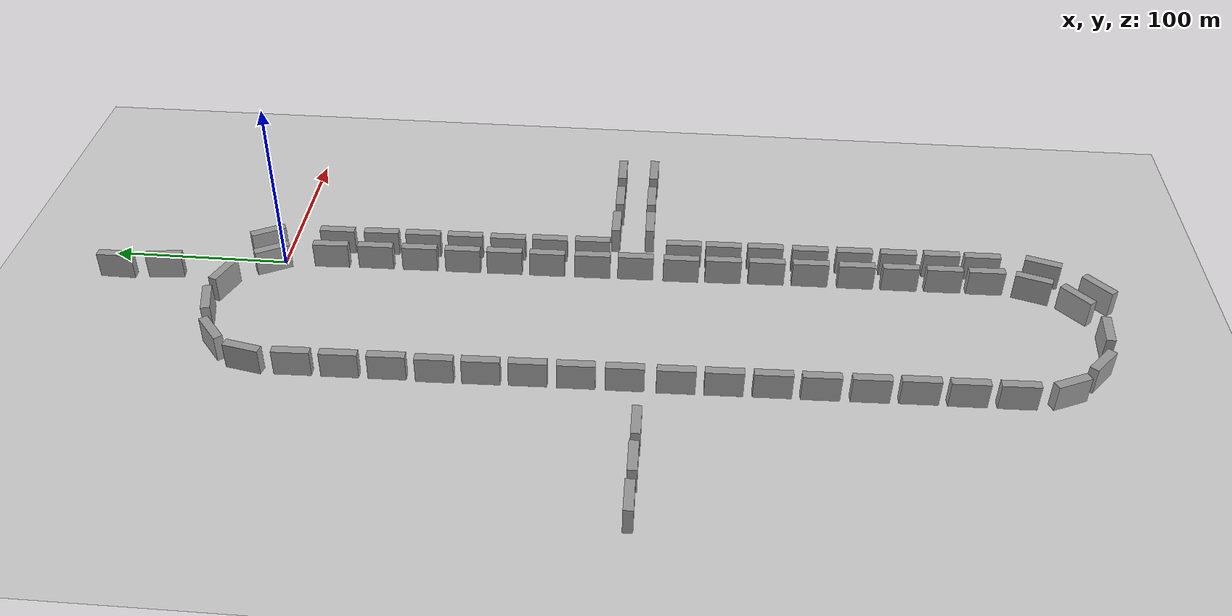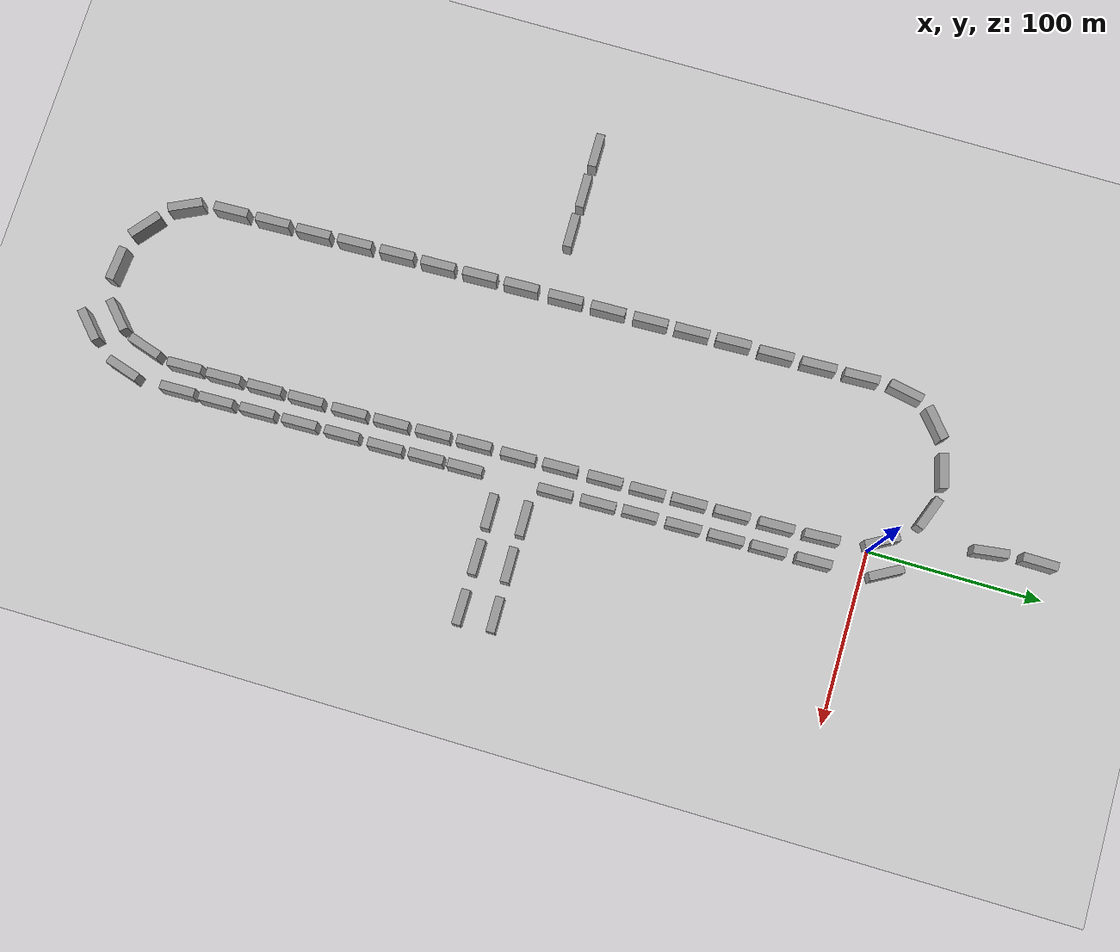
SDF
<sdf version="1.6">
 <world name="darpa_boxes">
  <model name="ground_plane">
   <static>1</static>
   <link name="link">
    <collision name="collision">
     <geometry><plane><normal>0 0 1</normal><size>2000 2000</size></plane></geometry>
     <surface>
      <contact><collide_bitmask>65535</collide_bitmask></contact>
      <friction><ode><mu>100</mu><mu2>50</mu2></ode></friction>
     </surface>
    </collision>
    <visual name="visual">
     <cast_shadows>0</cast_shadows>
     <geometry><plane><normal>0 0 1</normal><size>2000 2000</size></plane></geometry>
     <material>
      <script><uri>file://media/materials/scripts/gazebo.material</uri><name>Gazebo/Grey</name></script>
     </material>
    </visual>
   </link>
  </model>
  <light name="sun" type="directional">
   <pose>0 0 10 0 -0 0</pose>
   <diffuse>0.8 0.8 0.8 1</diffuse>
   <specular>0.2 0.2 0.2 1</specular>
   <attenuation>
    <range>1000</range>
    <constant>0.9</constant>
    <linear>0.01</linear>
    <quadratic>0.001</quadratic>
   </attenuation>
   <direction>-0.5 0.1 -0.9</direction>
  </light>
  <plugin name="rndf_gazebo_plugin0" filename="librndf_gazebo_plugin0.so.0.0.1">
   <rndf>darpa.rndf</rndf>
   <lanes>true</lanes>
   <waypoints>true</waypoints>
   <print_labels>true</print_labels>
  </plugin>
  <gravity>0 0 -9.8</gravity>
  <magnetic_field>6e-06 2.3e-05 -4.2e-05</magnetic_field>
  <atmosphere type="adiabatic"/>
  <physics name="default_physics" default="0" type="ode">
   <max_step_size>0.001</max_step_size>
   <real_time_factor>1</real_time_factor>
   <real_time_update_rate>1000</real_time_update_rate>
  </physics>
  <scene><ambient>0.4 0.4 0.4 1</ambient><background>0.7 0.7 0.7 1</background><shadows>1</shadows></scene>
  <spherical_coordinates>
   <surface_model>EARTH_WGS84</surface_model>
   <latitude_deg>0</latitude_deg>
   <longitude_deg>0</longitude_deg>
   <elevation>0</elevation>
   <heading_deg>0</heading_deg>
  </spherical_coordinates>
  <model name="long_box">
   <link name="link">
    <inertial>
     <mass>1</mass>
     <inertia>
      <ixx>0.166667</ixx>
      <ixy>0</ixy>
      <ixz>0</ixz>
      <iyy>0.166667</iyy>
      <iyz>0</iyz>
      <izz>0.166667</izz>
     </inertia>
     <pose>0 0 7.5 0 -0 0</pose>
    </inertial>
    <visual name="visual">
     <geometry><box><size>5 20 15</size></box></geometry>
     <material>
      <script><name>Gazebo/Grey</name><uri>file://media/materials/scripts/gazebo.material</uri></script>
      <shader type="vertex"><normal_map>__default__</normal_map></shader>
      <ambient>0.3 0.3 0.3 1</ambient>
      <diffuse>0.7 0.7 0.7 1</diffuse>
      <specular>0.01 0.01 0.01 1</specular>
      <emissive>0 0 0 1</emissive>
     </material>
     <pose>0 0 7.5 0 -0 0</pose>
    </visual>
    <collision name="collision">
     <pose>0 0 7.5 0 -0 0</pose>
     <geometry><box><size>5 20 15</size></box></geometry>
     <surface>
      <friction>
       <ode><mu>1</mu><mu2>1</mu2><fdir1>0 0 0</fdir1><slip1>0</slip1><slip2>0</slip2></ode>
       <torsional>
        <coefficient>1</coefficient>
        <patch_radius>0</patch_radius>
        <surface_radius>0</surface_radius>
        <use_patch_radius>1</use_patch_radius>
        <ode><slip>0</slip></ode>
       </torsional>
      </friction>
      <bounce><restitution_coefficient>0</restitution_coefficient><threshold>1e+06</threshold></bounce>
      <contact>
       <collide_without_contact>0</collide_without_contact>
       <collide_without_contact_bitmask>1</collide_without_contact_bitmask>
       <collide_bitmask>1</collide_bitmask>
       <ode>
        <soft_cfm>0</soft_cfm>
        <soft_erp>0.2</soft_erp>
        <kp>1e+13</kp>
        <kd>1</kd>
        <max_vel>0.01</max_vel>
        <min_depth>0</min_depth>
       </ode>
       <bullet>
        <split_impulse>1</split_impulse>
        <split_impulse_penetration_threshold>-0.01</split_impulse_penetration_threshold>
        <soft_cfm>0</soft_cfm>
        <soft_erp>0.2</soft_erp>
        <kp>1e+13</kp>
        <kd>1</kd>
       </bullet>
      </contact>
     </surface>
    </collision>
   </link>
   <static>1</static>
   <pose>1.32402 -27.3069 -0.049551 0.005043 -0.00022 0.043493</pose>
  </model>
  <model name="long_box_clone">
   <link name="link">
    <inertial>
     <mass>1</mass>
     <inertia>
      <ixx>0.166667</ixx>
      <ixy>0</ixy>
      <ixz>0</ixz>
      <iyy>0.166667</iyy>
      <iyz>0</iyz>
      <izz>0.166667</izz>
     </inertia>
     <pose>0 0 7.5 0 -0 0</pose>
    </inertial>
    <visual name="visual">
     <geometry><box><size>5 20 15</size></box></geometry>
     <material>
      <script><name>Gazebo/Grey</name><uri>file://media/materials/scripts/gazebo.material</uri></script>
      <shader type="vertex"><normal_map>__default__</normal_map></shader>
      <ambient>0.3 0.3 0.3 1</ambient>
      <diffuse>0.7 0.7 0.7 1</diffuse>
      <specular>0.01 0.01 0.01 1</specular>
      <emissive>0 0 0 1</emissive>
     </material>
     <pose>0 0 7.5 0 -0 0</pose>
    </visual>
    <collision name="collision">
     <pose>0 0 7.5 0 -0 0</pose>
     <geometry><box><size>5 20 15</size></box></geometry>
     <surface>
      <friction>
       <ode><mu>1</mu><mu2>1</mu2><fdir1>0 0 0</fdir1><slip1>0</slip1><slip2>0</slip2></ode>
       <torsional>
        <coefficient>1</coefficient>
        <patch_radius>0</patch_radius>
        <surface_radius>0</surface_radius>
        <use_patch_radius>1</use_patch_radius>
        <ode><slip>0</slip></ode>
       </torsional>
      </friction>
      <bounce><restitution_coefficient>0</restitution_coefficient><threshold>1e+06</threshold></bounce>
      <contact>
       <collide_without_contact>0</collide_without_contact>
       <collide_without_contact_bitmask>1</collide_without_contact_bitmask>
       <collide_bitmask>1</collide_bitmask>
       <ode>
        <soft_cfm>0</soft_cfm>
        <soft_erp>0.2</soft_erp>
        <kp>1e+13</kp>
        <kd>1</kd>
        <max_vel>0.01</max_vel>
        <min_depth>0</min_depth>
       </ode>
       <bullet>
        <split_impulse>1</split_impulse>
        <split_impulse_penetration_threshold>-0.01</split_impulse_penetration_threshold>
        <soft_cfm>0</soft_cfm>
        <soft_erp>0.2</soft_erp>
        <kp>1e+13</kp>
        <kd>1</kd>
       </bullet>
      </contact>
     </surface>
    </collision>
   </link>
   <static>1</static>
   <pose>2.2166 -52.9463 -0.049551 0.005047 -0.000114 0.022472</pose>
  </model>
  <model name="long_box_clone_clone">
   <link name="link">
    <inertial>
     <mass>1</mass>
     <inertia>
      <ixx>0.166667</ixx>
      <ixy>0</ixy>
      <ixz>0</ixz>
      <iyy>0.166667</iyy>
      <iyz>0</iyz>
      <izz>0.166667</izz>
     </inertia>
     <pose>0 0 7.5 0 -0 0</pose>
    </inertial>
    <visual name="visual">
     <geometry><box><size>5 20 15</size></box></geometry>
     <material>
      <script><name>Gazebo/Grey</name><uri>file://media/materials/scripts/gazebo.material</uri></script>
      <shader type="vertex"><normal_map>__default__</normal_map></shader>
      <ambient>0.3 0.3 0.3 1</ambient>
      <diffuse>0.7 0.7 0.7 1</diffuse>
      <specular>0.01 0.01 0.01 1</specular>
      <emissive>0 0 0 1</emissive>
     </material>
     <pose>0 0 7.5 0 -0 0</pose>
    </visual>
    <collision name="collision">
     <pose>0 0 7.5 0 -0 0</pose>
     <geometry><box><size>5 20 15</size></box></geometry>
     <surface>
      <friction>
       <ode><mu>1</mu><mu2>1</mu2><fdir1>0 0 0</fdir1><slip1>0</slip1><slip2>0</slip2></ode>
       <torsional>
        <coefficient>1</coefficient>
        <patch_radius>0</patch_radius>
        <surface_radius>0</surface_radius>
        <use_patch_radius>1</use_patch_radius>
        <ode><slip>0</slip></ode>
       </torsional>
      </friction>
      <bounce><restitution_coefficient>0</restitution_coefficient><threshold>1e+06</threshold></bounce>
      <contact>
       <collide_without_contact>0</collide_without_contact>
       <collide_without_contact_bitmask>1</collide_without_contact_bitmask>
       <collide_bitmask>1</collide_bitmask>
       <ode>
        <soft_cfm>0</soft_cfm>
        <soft_erp>0.2</soft_erp>
        <kp>1e+13</kp>
        <kd>1</kd>
        <max_vel>0.01</max_vel>
        <min_depth>0</min_depth>
       </ode>
       <bullet>
        <split_impulse>1</split_impulse>
        <split_impulse_penetration_threshold>-0.01</split_impulse_penetration_threshold>
        <soft_cfm>0</soft_cfm>
        <soft_erp>0.2</soft_erp>
        <kp>1e+13</kp>
        <kd>1</kd>
       </bullet>
      </contact>
     </surface>
    </collision>
   </link>
   <static>1</static>
   <pose>2.59574 -78.262 -0.049551 0.005047 -0.000114 0.022472</pose>
  </model>
  <model name="long_box_clone_clone_0">
   <link name="link">
    <inertial>
     <mass>1</mass>
     <inertia>
      <ixx>0.166667</ixx>
      <ixy>0</ixy>
      <ixz>0</ixz>
      <iyy>0.166667</iyy>
      <iyz>0</iyz>
      <izz>0.166667</izz>
     </inertia>
     <pose>0 0 7.5 0 -0 0</pose>
    </inertial>
    <visual name="visual">
     <geometry><box><size>5 20 15</size></box></geometry>
     <material>
      <script><name>Gazebo/Grey</name><uri>file://media/materials/scripts/gazebo.material</uri></script>
      <shader type="vertex"><normal_map>__default__</normal_map></shader>
      <ambient>0.3 0.3 0.3 1</ambient>
      <diffuse>0.7 0.7 0.7 1</diffuse>
      <specular>0.01 0.01 0.01 1</specular>
      <emissive>0 0 0 1</emissive>
     </material>
     <pose>0 0 7.5 0 -0 0</pose>
    </visual>
    <collision name="collision">
     <pose>0 0 7.5 0 -0 0</pose>
     <geometry><box><size>5 20 15</size></box></geometry>
     <surface>
      <friction>
       <ode><mu>1</mu><mu2>1</mu2><fdir1>0 0 0</fdir1><slip1>0</slip1><slip2>0</slip2></ode>
       <torsional>
        <coefficient>1</coefficient>
        <patch_radius>0</patch_radius>
        <surface_radius>0</surface_radius>
        <use_patch_radius>1</use_patch_radius>
        <ode><slip>0</slip></ode>
       </torsional>
      </friction>
      <bounce><restitution_coefficient>0</restitution_coefficient><threshold>1e+06</threshold></bounce>
      <contact>
       <collide_without_contact>0</collide_without_contact>
       <collide_without_contact_bitmask>1</collide_without_contact_bitmask>
       <collide_bitmask>1</collide_bitmask>
       <ode>
        <soft_cfm>0</soft_cfm>
        <soft_erp>0.2</soft_erp>
        <kp>1e+13</kp>
        <kd>1</kd>
        <max_vel>0.01</max_vel>
        <min_depth>0</min_depth>
       </ode>
       <bullet>
        <split_impulse>1</split_impulse>
        <split_impulse_penetration_threshold>-0.01</split_impulse_penetration_threshold>
        <soft_cfm>0</soft_cfm>
        <soft_erp>0.2</soft_erp>
        <kp>1e+13</kp>
        <kd>1</kd>
       </bullet>
      </contact>
     </surface>
    </collision>
   </link>
   <static>1</static>
   <pose>2.95301 -102.999 -0.049551 0.005047 -0.000114 0.022472</pose>
  </model>
  <model name="long_box_clone_clone_1">
   <link name="link">
    <inertial>
     <mass>1</mass>
     <inertia>
      <ixx>0.166667</ixx>
      <ixy>0</ixy>
      <ixz>0</ixz>
      <iyy>0.166667</iyy>
      <iyz>0</iyz>
      <izz>0.166667</izz>
     </inertia>
     <pose>0 0 7.5 0 -0 0</pose>
    </inertial>
    <visual name="visual">
     <geometry><box><size>5 20 15</size></box></geometry>
     <material>
      <script><name>Gazebo/Grey</name><uri>file://media/materials/scripts/gazebo.material</uri></script>
      <shader type="vertex"><normal_map>__default__</normal_map></shader>
      <ambient>0.3 0.3 0.3 1</ambient>
      <diffuse>0.7 0.7 0.7 1</diffuse>
      <specular>0.01 0.01 0.01 1</specular>
      <emissive>0 0 0 1</emissive>
     </material>
     <pose>0 0 7.5 0 -0 0</pose>
    </visual>
    <collision name="collision">
     <pose>0 0 7.5 0 -0 0</pose>
     <geometry><box><size>5 20 15</size></box></geometry>
     <surface>
      <friction>
       <ode><mu>1</mu><mu2>1</mu2><fdir1>0 0 0</fdir1><slip1>0</slip1><slip2>0</slip2></ode>
       <torsional>
        <coefficient>1</coefficient>
        <patch_radius>0</patch_radius>
        <surface_radius>0</surface_radius>
        <use_patch_radius>1</use_patch_radius>
        <ode><slip>0</slip></ode>
       </torsional>
      </friction>
      <bounce><restitution_coefficient>0</restitution_coefficient><threshold>1e+06</threshold></bounce>
      <contact>
       <collide_without_contact>0</collide_without_contact>
       <collide_without_contact_bitmask>1</collide_without_contact_bitmask>
       <collide_bitmask>1</collide_bitmask>
       <ode>
        <soft_cfm>0</soft_cfm>
        <soft_erp>0.2</soft_erp>
        <kp>1e+13</kp>
        <kd>1</kd>
        <max_vel>0.01</max_vel>
        <min_depth>0</min_depth>
       </ode>
       <bullet>
        <split_impulse>1</split_impulse>
        <split_impulse_penetration_threshold>-0.01</split_impulse_penetration_threshold>
        <soft_cfm>0</soft_cfm>
        <soft_erp>0.2</soft_erp>
        <kp>1e+13</kp>
        <kd>1</kd>
       </bullet>
      </contact>
     </surface>
    </collision>
   </link>
   <static>1</static>
   <pose>3.43621 -126.848 -0.049551 0.005047 -0.000114 0.022472</pose>
  </model>
  <model name="long_box_clone_clone_2">
   <link name="link">
    <inertial>
     <mass>1</mass>
     <inertia>
      <ixx>0.166667</ixx>
      <ixy>0</ixy>
      <ixz>0</ixz>
      <iyy>0.166667</iyy>
      <iyz>0</iyz>
      <izz>0.166667</izz>
     </inertia>
     <pose>0 0 7.5 0 -0 0</pose>
    </inertial>
    <visual name="visual">
     <geometry><box><size>5 20 15</size></box></geometry>
     <material>
      <script><name>Gazebo/Grey</name><uri>file://media/materials/scripts/gazebo.material</uri></script>
      <shader type="vertex"><normal_map>__default__</normal_map></shader>
      <ambient>0.3 0.3 0.3 1</ambient>
      <diffuse>0.7 0.7 0.7 1</diffuse>
      <specular>0.01 0.01 0.01 1</specular>
      <emissive>0 0 0 1</emissive>
     </material>
     <pose>0 0 7.5 0 -0 0</pose>
    </visual>
    <collision name="collision">
     <pose>0 0 7.5 0 -0 0</pose>
     <geometry><box><size>5 20 15</size></box></geometry>
     <surface>
      <friction>
       <ode><mu>1</mu><mu2>1</mu2><fdir1>0 0 0</fdir1><slip1>0</slip1><slip2>0</slip2></ode>
       <torsional>
        <coefficient>1</coefficient>
        <patch_radius>0</patch_radius>
        <surface_radius>0</surface_radius>
        <use_patch_radius>1</use_patch_radius>
        <ode><slip>0</slip></ode>
       </torsional>
      </friction>
      <bounce><restitution_coefficient>0</restitution_coefficient><threshold>1e+06</threshold></bounce>
      <contact>
       <collide_without_contact>0</collide_without_contact>
       <collide_without_contact_bitmask>1</collide_without_contact_bitmask>
       <collide_bitmask>1</collide_bitmask>
       <ode>
        <soft_cfm>0</soft_cfm>
        <soft_erp>0.2</soft_erp>
        <kp>1e+13</kp>
        <kd>1</kd>
        <max_vel>0.01</max_vel>
        <min_depth>0</min_depth>
       </ode>
       <bullet>
        <split_impulse>1</split_impulse>
        <split_impulse_penetration_threshold>-0.01</split_impulse_penetration_threshold>
        <soft_cfm>0</soft_cfm>
        <soft_erp>0.2</soft_erp>
        <kp>1e+13</kp>
        <kd>1</kd>
       </bullet>
      </contact>
     </surface>
    </collision>
   </link>
   <static>1</static>
   <pose>3.68929 -151.222 -0.049551 0.005047 -0.000114 0.022472</pose>
  </model>
  <model name="long_box_clone_clone_3">
   <link name="link">
    <inertial>
     <mass>1</mass>
     <inertia>
      <ixx>0.166667</ixx>
      <ixy>0</ixy>
      <ixz>0</ixz>
      <iyy>0.166667</iyy>
      <iyz>0</iyz>
      <izz>0.166667</izz>
     </inertia>
     <pose>0 0 7.5 0 -0 0</pose>
    </inertial>
    <visual name="visual">
     <geometry><box><size>5 20 15</size></box></geometry>
     <material>
      <script><name>Gazebo/Grey</name><uri>file://media/materials/scripts/gazebo.material</uri></script>
      <shader type="vertex"><normal_map>__default__</normal_map></shader>
      <ambient>0.3 0.3 0.3 1</ambient>
      <diffuse>0.7 0.7 0.7 1</diffuse>
      <specular>0.01 0.01 0.01 1</specular>
      <emissive>0 0 0 1</emissive>
     </material>
     <pose>0 0 7.5 0 -0 0</pose>
    </visual>
    <collision name="collision">
     <pose>0 0 7.5 0 -0 0</pose>
     <geometry><box><size>5 20 15</size></box></geometry>
     <surface>
      <friction>
       <ode><mu>1</mu><mu2>1</mu2><fdir1>0 0 0</fdir1><slip1>0</slip1><slip2>0</slip2></ode>
       <torsional>
        <coefficient>1</coefficient>
        <patch_radius>0</patch_radius>
        <surface_radius>0</surface_radius>
        <use_patch_radius>1</use_patch_radius>
        <ode><slip>0</slip></ode>
       </torsional>
      </friction>
      <bounce><restitution_coefficient>0</restitution_coefficient><threshold>1e+06</threshold></bounce>
      <contact>
       <collide_without_contact>0</collide_without_contact>
       <collide_without_contact_bitmask>1</collide_without_contact_bitmask>
       <collide_bitmask>1</collide_bitmask>
       <ode>
        <soft_cfm>0</soft_cfm>
        <soft_erp>0.2</soft_erp>
        <kp>1e+13</kp>
        <kd>1</kd>
        <max_vel>0.01</max_vel>
        <min_depth>0</min_depth>
       </ode>
       <bullet>
        <split_impulse>1</split_impulse>
        <split_impulse_penetration_threshold>-0.01</split_impulse_penetration_threshold>
        <soft_cfm>0</soft_cfm>
        <soft_erp>0.2</soft_erp>
        <kp>1e+13</kp>
        <kd>1</kd>
       </bullet>
      </contact>
     </surface>
    </collision>
   </link>
   <static>1</static>
   <pose>4.1621 -176.965 -0.049551 0.005047 -0.000114 0.022472</pose>
  </model>
  <model name="long_box_clone_clone_4">
   <link name="link">
    <inertial>
     <mass>1</mass>
     <inertia>
      <ixx>0.166667</ixx>
      <ixy>0</ixy>
      <ixz>0</ixz>
      <iyy>0.166667</iyy>
      <iyz>0</iyz>
      <izz>0.166667</izz>
     </inertia>
     <pose>0 0 7.5 0 -0 0</pose>
    </inertial>
    <visual name="visual">
     <geometry><box><size>5 20 15</size></box></geometry>
     <material>
      <script><name>Gazebo/Grey</name><uri>file://media/materials/scripts/gazebo.material</uri></script>
      <shader type="vertex"><normal_map>__default__</normal_map></shader>
      <ambient>0.3 0.3 0.3 1</ambient>
      <diffuse>0.7 0.7 0.7 1</diffuse>
      <specular>0.01 0.01 0.01 1</specular>
      <emissive>0 0 0 1</emissive>
     </material>
     <pose>0 0 7.5 0 -0 0</pose>
    </visual>
    <collision name="collision">
     <pose>0 0 7.5 0 -0 0</pose>
     <geometry><box><size>5 20 15</size></box></geometry>
     <surface>
      <friction>
       <ode><mu>1</mu><mu2>1</mu2><fdir1>0 0 0</fdir1><slip1>0</slip1><slip2>0</slip2></ode>
       <torsional>
        <coefficient>1</coefficient>
        <patch_radius>0</patch_radius>
        <surface_radius>0</surface_radius>
        <use_patch_radius>1</use_patch_radius>
        <ode><slip>0</slip></ode>
       </torsional>
      </friction>
      <bounce><restitution_coefficient>0</restitution_coefficient><threshold>1e+06</threshold></bounce>
      <contact>
       <collide_without_contact>0</collide_without_contact>
       <collide_without_contact_bitmask>1</collide_without_contact_bitmask>
       <collide_bitmask>1</collide_bitmask>
       <ode>
        <soft_cfm>0</soft_cfm>
        <soft_erp>0.2</soft_erp>
        <kp>1e+13</kp>
        <kd>1</kd>
        <max_vel>0.01</max_vel>
        <min_depth>0</min_depth>
       </ode>
       <bullet>
        <split_impulse>1</split_impulse>
        <split_impulse_penetration_threshold>-0.01</split_impulse_penetration_threshold>
        <soft_cfm>0</soft_cfm>
        <soft_erp>0.2</soft_erp>
        <kp>1e+13</kp>
        <kd>1</kd>
       </bullet>
      </contact>
     </surface>
    </collision>
   </link>
   <static>1</static>
   <pose>4.69386 -201.317 -0.049551 0.005047 -0.000114 0.022472</pose>
  </model>
  <model name="long_box_clone_clone_5">
   <link name="link">
    <inertial>
     <mass>1</mass>
     <inertia>
      <ixx>0.166667</ixx>
      <ixy>0</ixy>
      <ixz>0</ixz>
      <iyy>0.166667</iyy>
      <iyz>0</iyz>
      <izz>0.166667</izz>
     </inertia>
     <pose>0 0 7.5 0 -0 0</pose>
    </inertial>
    <visual name="visual">
     <geometry><box><size>5 20 15</size></box></geometry>
     <material>
      <script><name>Gazebo/Grey</name><uri>file://media/materials/scripts/gazebo.material</uri></script>
      <shader type="vertex"><normal_map>__default__</normal_map></shader>
      <ambient>0.3 0.3 0.3 1</ambient>
      <diffuse>0.7 0.7 0.7 1</diffuse>
      <specular>0.01 0.01 0.01 1</specular>
      <emissive>0 0 0 1</emissive>
     </material>
     <pose>0 0 7.5 0 -0 0</pose>
    </visual>
    <collision name="collision">
     <pose>0 0 7.5 0 -0 0</pose>
     <geometry><box><size>5 20 15</size></box></geometry>
     <surface>
      <friction>
       <ode><mu>1</mu><mu2>1</mu2><fdir1>0 0 0</fdir1><slip1>0</slip1><slip2>0</slip2></ode>
       <torsional>
        <coefficient>1</coefficient>
        <patch_radius>0</patch_radius>
        <surface_radius>0</surface_radius>
        <use_patch_radius>1</use_patch_radius>
        <ode><slip>0</slip></ode>
       </torsional>
      </friction>
      <bounce><restitution_coefficient>0</restitution_coefficient><threshold>1e+06</threshold></bounce>
      <contact>
       <collide_without_contact>0</collide_without_contact>
       <collide_without_contact_bitmask>1</collide_without_contact_bitmask>
       <collide_bitmask>1</collide_bitmask>
       <ode>
        <soft_cfm>0</soft_cfm>
        <soft_erp>0.2</soft_erp>
        <kp>1e+13</kp>
        <kd>1</kd>
        <max_vel>0.01</max_vel>
        <min_depth>0</min_depth>
       </ode>
       <bullet>
        <split_impulse>1</split_impulse>
        <split_impulse_penetration_threshold>-0.01</split_impulse_penetration_threshold>
        <soft_cfm>0</soft_cfm>
        <soft_erp>0.2</soft_erp>
        <kp>1e+13</kp>
        <kd>1</kd>
       </bullet>
      </contact>
     </surface>
    </collision>
   </link>
   <static>1</static>
   <pose>4.85871 -226.99 -0.049551 0.005047 -0.000114 0.022472</pose>
  </model>
  <model name="long_box_clone_clone_6">
   <link name="link">
    <inertial>
     <mass>1</mass>
     <inertia>
      <ixx>0.166667</ixx>
      <ixy>0</ixy>
      <ixz>0</ixz>
      <iyy>0.166667</iyy>
      <iyz>0</iyz>
      <izz>0.166667</izz>
     </inertia>
     <pose>0 0 7.5 0 -0 0</pose>
    </inertial>
    <visual name="visual">
     <geometry><box><size>5 20 15</size></box></geometry>
     <material>
      <script><name>Gazebo/Grey</name><uri>file://media/materials/scripts/gazebo.material</uri></script>
      <shader type="vertex"><normal_map>__default__</normal_map></shader>
      <ambient>0.3 0.3 0.3 1</ambient>
      <diffuse>0.7 0.7 0.7 1</diffuse>
      <specular>0.01 0.01 0.01 1</specular>
      <emissive>0 0 0 1</emissive>
     </material>
     <pose>0 0 7.5 0 -0 0</pose>
    </visual>
    <collision name="collision">
     <pose>0 0 7.5 0 -0 0</pose>
     <geometry><box><size>5 20 15</size></box></geometry>
     <surface>
      <friction>
       <ode><mu>1</mu><mu2>1</mu2><fdir1>0 0 0</fdir1><slip1>0</slip1><slip2>0</slip2></ode>
       <torsional>
        <coefficient>1</coefficient>
        <patch_radius>0</patch_radius>
        <surface_radius>0</surface_radius>
        <use_patch_radius>1</use_patch_radius>
        <ode><slip>0</slip></ode>
       </torsional>
      </friction>
      <bounce><restitution_coefficient>0</restitution_coefficient><threshold>1e+06</threshold></bounce>
      <contact>
       <collide_without_contact>0</collide_without_contact>
       <collide_without_contact_bitmask>1</collide_without_contact_bitmask>
       <collide_bitmask>1</collide_bitmask>
       <ode>
        <soft_cfm>0</soft_cfm>
        <soft_erp>0.2</soft_erp>
        <kp>1e+13</kp>
        <kd>1</kd>
        <max_vel>0.01</max_vel>
        <min_depth>0</min_depth>
       </ode>
       <bullet>
        <split_impulse>1</split_impulse>
        <split_impulse_penetration_threshold>-0.01</split_impulse_penetration_threshold>
        <soft_cfm>0</soft_cfm>
        <soft_erp>0.2</soft_erp>
        <kp>1e+13</kp>
        <kd>1</kd>
       </bullet>
      </contact>
     </surface>
    </collision>
   </link>
   <static>1</static>
   <pose>5.67981 -250.633 -0.049551 0.005047 -0.000114 0.022472</pose>
  </model>
  <model name="long_box_clone_clone_7">
   <link name="link">
    <inertial>
     <mass>1</mass>
     <inertia>
      <ixx>0.166667</ixx>
      <ixy>0</ixy>
      <ixz>0</ixz>
      <iyy>0.166667</iyy>
      <iyz>0</iyz>
      <izz>0.166667</izz>
     </inertia>
     <pose>0 0 7.5 0 -0 0</pose>
    </inertial>
    <visual name="visual">
     <geometry><box><size>5 20 15</size></box></geometry>
     <material>
      <script><name>Gazebo/Grey</name><uri>file://media/materials/scripts/gazebo.material</uri></script>
      <shader type="vertex"><normal_map>__default__</normal_map></shader>
      <ambient>0.3 0.3 0.3 1</ambient>
      <diffuse>0.7 0.7 0.7 1</diffuse>
      <specular>0.01 0.01 0.01 1</specular>
      <emissive>0 0 0 1</emissive>
     </material>
     <pose>0 0 7.5 0 -0 0</pose>
    </visual>
    <collision name="collision">
     <pose>0 0 7.5 0 -0 0</pose>
     <geometry><box><size>5 20 15</size></box></geometry>
     <surface>
      <friction>
       <ode><mu>1</mu><mu2>1</mu2><fdir1>0 0 0</fdir1><slip1>0</slip1><slip2>0</slip2></ode>
       <torsional>
        <coefficient>1</coefficient>
        <patch_radius>0</patch_radius>
        <surface_radius>0</surface_radius>
        <use_patch_radius>1</use_patch_radius>
        <ode><slip>0</slip></ode>
       </torsional>
      </friction>
      <bounce><restitution_coefficient>0</restitution_coefficient><threshold>1e+06</threshold></bounce>
      <contact>
       <collide_without_contact>0</collide_without_contact>
       <collide_without_contact_bitmask>1</collide_without_contact_bitmask>
       <collide_bitmask>1</collide_bitmask>
       <ode>
        <soft_cfm>0</soft_cfm>
        <soft_erp>0.2</soft_erp>
        <kp>1e+13</kp>
        <kd>1</kd>
        <max_vel>0.01</max_vel>
        <min_depth>0</min_depth>
       </ode>
       <bullet>
        <split_impulse>1</split_impulse>
        <split_impulse_penetration_threshold>-0.01</split_impulse_penetration_threshold>
        <soft_cfm>0</soft_cfm>
        <soft_erp>0.2</soft_erp>
        <kp>1e+13</kp>
        <kd>1</kd>
       </bullet>
      </contact>
     </surface>
    </collision>
   </link>
   <static>1</static>
   <pose>6.45947 -274.93 -0.049551 0.005047 -0.000114 0.022472</pose>
  </model>
  <model name="long_box_clone_clone_8">
   <link name="link">
    <inertial>
     <mass>1</mass>
     <inertia>
      <ixx>0.166667</ixx>
      <ixy>0</ixy>
      <ixz>0</ixz>
      <iyy>0.166667</iyy>
      <iyz>0</iyz>
      <izz>0.166667</izz>
     </inertia>
     <pose>0 0 7.5 0 -0 0</pose>
    </inertial>
    <visual name="visual">
     <geometry><box><size>5 20 15</size></box></geometry>
     <material>
      <script><name>Gazebo/Grey</name><uri>file://media/materials/scripts/gazebo.material</uri></script>
      <shader type="vertex"><normal_map>__default__</normal_map></shader>
      <ambient>0.3 0.3 0.3 1</ambient>
      <diffuse>0.7 0.7 0.7 1</diffuse>
      <specular>0.01 0.01 0.01 1</specular>
      <emissive>0 0 0 1</emissive>
     </material>
     <pose>0 0 7.5 0 -0 0</pose>
    </visual>
    <collision name="collision">
     <pose>0 0 7.5 0 -0 0</pose>
     <geometry><box><size>5 20 15</size></box></geometry>
     <surface>
      <friction>
       <ode><mu>1</mu><mu2>1</mu2><fdir1>0 0 0</fdir1><slip1>0</slip1><slip2>0</slip2></ode>
       <torsional>
        <coefficient>1</coefficient>
        <patch_radius>0</patch_radius>
        <surface_radius>0</surface_radius>
        <use_patch_radius>1</use_patch_radius>
        <ode><slip>0</slip></ode>
       </torsional>
      </friction>
      <bounce><restitution_coefficient>0</restitution_coefficient><threshold>1e+06</threshold></bounce>
      <contact>
       <collide_without_contact>0</collide_without_contact>
       <collide_without_contact_bitmask>1</collide_without_contact_bitmask>
       <collide_bitmask>1</collide_bitmask>
       <ode>
        <soft_cfm>0</soft_cfm>
        <soft_erp>0.2</soft_erp>
        <kp>1e+13</kp>
        <kd>1</kd>
        <max_vel>0.01</max_vel>
        <min_depth>0</min_depth>
       </ode>
       <bullet>
        <split_impulse>1</split_impulse>
        <split_impulse_penetration_threshold>-0.01</split_impulse_penetration_threshold>
        <soft_cfm>0</soft_cfm>
        <soft_erp>0.2</soft_erp>
        <kp>1e+13</kp>
        <kd>1</kd>
       </bullet>
      </contact>
     </surface>
    </collision>
   </link>
   <static>1</static>
   <pose>6.96106 -299.323 -0.049551 0.005047 -0.000114 0.022472</pose>
  </model>
  <model name="long_box_clone_clone_9">
   <link name="link">
    <inertial>
     <mass>1</mass>
     <inertia>
      <ixx>0.166667</ixx>
      <ixy>0</ixy>
      <ixz>0</ixz>
      <iyy>0.166667</iyy>
      <iyz>0</iyz>
      <izz>0.166667</izz>
     </inertia>
     <pose>0 0 7.5 0 -0 0</pose>
    </inertial>
    <visual name="visual">
     <geometry><box><size>5 20 15</size></box></geometry>
     <material>
      <script><name>Gazebo/Grey</name><uri>file://media/materials/scripts/gazebo.material</uri></script>
      <shader type="vertex"><normal_map>__default__</normal_map></shader>
      <ambient>0.3 0.3 0.3 1</ambient>
      <diffuse>0.7 0.7 0.7 1</diffuse>
      <specular>0.01 0.01 0.01 1</specular>
      <emissive>0 0 0 1</emissive>
     </material>
     <pose>0 0 7.5 0 -0 0</pose>
    </visual>
    <collision name="collision">
     <pose>0 0 7.5 0 -0 0</pose>
     <geometry><box><size>5 20 15</size></box></geometry>
     <surface>
      <friction>
       <ode><mu>1</mu><mu2>1</mu2><fdir1>0 0 0</fdir1><slip1>0</slip1><slip2>0</slip2></ode>
       <torsional>
        <coefficient>1</coefficient>
        <patch_radius>0</patch_radius>
        <surface_radius>0</surface_radius>
        <use_patch_radius>1</use_patch_radius>
        <ode><slip>0</slip></ode>
       </torsional>
      </friction>
      <bounce><restitution_coefficient>0</restitution_coefficient><threshold>1e+06</threshold></bounce>
      <contact>
       <collide_without_contact>0</collide_without_contact>
       <collide_without_contact_bitmask>1</collide_without_contact_bitmask>
       <collide_bitmask>1</collide_bitmask>
       <ode>
        <soft_cfm>0</soft_cfm>
        <soft_erp>0.2</soft_erp>
        <kp>1e+13</kp>
        <kd>1</kd>
        <max_vel>0.01</max_vel>
        <min_depth>0</min_depth>
       </ode>
       <bullet>
        <split_impulse>1</split_impulse>
        <split_impulse_penetration_threshold>-0.01</split_impulse_penetration_threshold>
        <soft_cfm>0</soft_cfm>
        <soft_erp>0.2</soft_erp>
        <kp>1e+13</kp>
        <kd>1</kd>
       </bullet>
      </contact>
     </surface>
    </collision>
   </link>
   <static>1</static>
   <pose>7.18976 -324.823 -0.049551 0.005047 -0.000114 0.022472</pose>
  </model>
  <model name="long_box_clone_clone_10">
   <link name="link">
    <inertial>
     <mass>1</mass>
     <inertia>
      <ixx>0.166667</ixx>
      <ixy>0</ixy>
      <ixz>0</ixz>
      <iyy>0.166667</iyy>
      <iyz>0</iyz>
      <izz>0.166667</izz>
     </inertia>
     <pose>0 0 7.5 0 -0 0</pose>
    </inertial>
    <visual name="visual">
     <geometry><box><size>5 20 15</size></box></geometry>
     <material>
      <script><name>Gazebo/Grey</name><uri>file://media/materials/scripts/gazebo.material</uri></script>
      <shader type="vertex"><normal_map>__default__</normal_map></shader>
      <ambient>0.3 0.3 0.3 1</ambient>
      <diffuse>0.7 0.7 0.7 1</diffuse>
      <specular>0.01 0.01 0.01 1</specular>
      <emissive>0 0 0 1</emissive>
     </material>
     <pose>0 0 7.5 0 -0 0</pose>
    </visual>
    <collision name="collision">
     <pose>0 0 7.5 0 -0 0</pose>
     <geometry><box><size>5 20 15</size></box></geometry>
     <surface>
      <friction>
       <ode><mu>1</mu><mu2>1</mu2><fdir1>0 0 0</fdir1><slip1>0</slip1><slip2>0</slip2></ode>
       <torsional>
        <coefficient>1</coefficient>
        <patch_radius>0</patch_radius>
        <surface_radius>0</surface_radius>
        <use_patch_radius>1</use_patch_radius>
        <ode><slip>0</slip></ode>
       </torsional>
      </friction>
      <bounce><restitution_coefficient>0</restitution_coefficient><threshold>1e+06</threshold></bounce>
      <contact>
       <collide_without_contact>0</collide_without_contact>
       <collide_without_contact_bitmask>1</collide_without_contact_bitmask>
       <collide_bitmask>1</collide_bitmask>
       <ode>
        <soft_cfm>0</soft_cfm>
        <soft_erp>0.2</soft_erp>
        <kp>1e+13</kp>
        <kd>1</kd>
        <max_vel>0.01</max_vel>
        <min_depth>0</min_depth>
       </ode>
       <bullet>
        <split_impulse>1</split_impulse>
        <split_impulse_penetration_threshold>-0.01</split_impulse_penetration_threshold>
        <soft_cfm>0</soft_cfm>
        <soft_erp>0.2</soft_erp>
        <kp>1e+13</kp>
        <kd>1</kd>
       </bullet>
      </contact>
     </surface>
    </collision>
   </link>
   <static>1</static>
   <pose>7.48707 -349.113 -0.049551 0.005047 -0.000114 0.022472</pose>
  </model>
  <model name="long_box_clone_clone_11">
   <link name="link">
    <inertial>
     <mass>1</mass>
     <inertia>
      <ixx>0.166667</ixx>
      <ixy>0</ixy>
      <ixz>0</ixz>
      <iyy>0.166667</iyy>
      <iyz>0</iyz>
      <izz>0.166667</izz>
     </inertia>
     <pose>0 0 7.5 0 -0 0</pose>
    </inertial>
    <visual name="visual">
     <geometry><box><size>5 20 15</size></box></geometry>
     <material>
      <script><name>Gazebo/Grey</name><uri>file://media/materials/scripts/gazebo.material</uri></script>
      <shader type="vertex"><normal_map>__default__</normal_map></shader>
      <ambient>0.3 0.3 0.3 1</ambient>
      <diffuse>0.7 0.7 0.7 1</diffuse>
      <specular>0.01 0.01 0.01 1</specular>
      <emissive>0 0 0 1</emissive>
     </material>
     <pose>0 0 7.5 0 -0 0</pose>
    </visual>
    <collision name="collision">
     <pose>0 0 7.5 0 -0 0</pose>
     <geometry><box><size>5 20 15</size></box></geometry>
     <surface>
      <friction>
       <ode><mu>1</mu><mu2>1</mu2><fdir1>0 0 0</fdir1><slip1>0</slip1><slip2>0</slip2></ode>
       <torsional>
        <coefficient>1</coefficient>
        <patch_radius>0</patch_radius>
        <surface_radius>0</surface_radius>
        <use_patch_radius>1</use_patch_radius>
        <ode><slip>0</slip></ode>
       </torsional>
      </friction>
      <bounce><restitution_coefficient>0</restitution_coefficient><threshold>1e+06</threshold></bounce>
      <contact>
       <collide_without_contact>0</collide_without_contact>
       <collide_without_contact_bitmask>1</collide_without_contact_bitmask>
       <collide_bitmask>1</collide_bitmask>
       <ode>
        <soft_cfm>0</soft_cfm>
        <soft_erp>0.2</soft_erp>
        <kp>1e+13</kp>
        <kd>1</kd>
        <max_vel>0.01</max_vel>
        <min_depth>0</min_depth>
       </ode>
       <bullet>
        <split_impulse>1</split_impulse>
        <split_impulse_penetration_threshold>-0.01</split_impulse_penetration_threshold>
        <soft_cfm>0</soft_cfm>
        <soft_erp>0.2</soft_erp>
        <kp>1e+13</kp>
        <kd>1</kd>
       </bullet>
      </contact>
     </surface>
    </collision>
   </link>
   <static>1</static>
   <pose>7.93072 -373.289 -0.049551 0.005047 -0.000114 0.022472</pose>
  </model>
  <model name="long_box_clone_clone_12">
   <link name="link">
    <inertial>
     <mass>1</mass>
     <inertia>
      <ixx>0.166667</ixx>
      <ixy>0</ixy>
      <ixz>0</ixz>
      <iyy>0.166667</iyy>
      <iyz>0</iyz>
      <izz>0.166667</izz>
     </inertia>
     <pose>0 0 7.5 0 -0 0</pose>
    </inertial>
    <visual name="visual">
     <geometry><box><size>5 20 15</size></box></geometry>
     <material>
      <script><name>Gazebo/Grey</name><uri>file://media/materials/scripts/gazebo.material</uri></script>
      <shader type="vertex"><normal_map>__default__</normal_map></shader>
      <ambient>0.3 0.3 0.3 1</ambient>
      <diffuse>0.7 0.7 0.7 1</diffuse>
      <specular>0.01 0.01 0.01 1</specular>
      <emissive>0 0 0 1</emissive>
     </material>
     <pose>0 0 7.5 0 -0 0</pose>
    </visual>
    <collision name="collision">
     <pose>0 0 7.5 0 -0 0</pose>
     <geometry><box><size>5 20 15</size></box></geometry>
     <surface>
      <friction>
       <ode><mu>1</mu><mu2>1</mu2><fdir1>0 0 0</fdir1><slip1>0</slip1><slip2>0</slip2></ode>
       <torsional>
        <coefficient>1</coefficient>
        <patch_radius>0</patch_radius>
        <surface_radius>0</surface_radius>
        <use_patch_radius>1</use_patch_radius>
        <ode><slip>0</slip></ode>
       </torsional>
      </friction>
      <bounce><restitution_coefficient>0</restitution_coefficient><threshold>1e+06</threshold></bounce>
      <contact>
       <collide_without_contact>0</collide_without_contact>
       <collide_without_contact_bitmask>1</collide_without_contact_bitmask>
       <collide_bitmask>1</collide_bitmask>
       <ode>
        <soft_cfm>0</soft_cfm>
        <soft_erp>0.2</soft_erp>
        <kp>1e+13</kp>
        <kd>1</kd>
        <max_vel>0.01</max_vel>
        <min_depth>0</min_depth>
       </ode>
       <bullet>
        <split_impulse>1</split_impulse>
        <split_impulse_penetration_threshold>-0.01</split_impulse_penetration_threshold>
        <soft_cfm>0</soft_cfm>
        <soft_erp>0.2</soft_erp>
        <kp>1e+13</kp>
        <kd>1</kd>
       </bullet>
      </contact>
     </surface>
    </collision>
   </link>
   <static>1</static>
   <pose>8.01915 -396.284 -0.049551 0.005047 -0.000114 0.022472</pose>
  </model>
  <model name="long_box_clone_clone_13">
   <link name="link">
    <inertial>
     <mass>1</mass>
     <inertia>
      <ixx>0.166667</ixx>
      <ixy>0</ixy>
      <ixz>0</ixz>
      <iyy>0.166667</iyy>
      <iyz>0</iyz>
      <izz>0.166667</izz>
     </inertia>
     <pose>0 0 7.5 0 -0 0</pose>
    </inertial>
    <visual name="visual">
     <geometry><box><size>5 20 15</size></box></geometry>
     <material>
      <script><name>Gazebo/Grey</name><uri>file://media/materials/scripts/gazebo.material</uri></script>
      <shader type="vertex"><normal_map>__default__</normal_map></shader>
      <ambient>0.3 0.3 0.3 1</ambient>
      <diffuse>0.7 0.7 0.7 1</diffuse>
      <specular>0.01 0.01 0.01 1</specular>
      <emissive>0 0 0 1</emissive>
     </material>
     <pose>0 0 7.5 0 -0 0</pose>
    </visual>
    <collision name="collision">
     <pose>0 0 7.5 0 -0 0</pose>
     <geometry><box><size>5 20 15</size></box></geometry>
     <surface>
      <friction>
       <ode><mu>1</mu><mu2>1</mu2><fdir1>0 0 0</fdir1><slip1>0</slip1><slip2>0</slip2></ode>
       <torsional>
        <coefficient>1</coefficient>
        <patch_radius>0</patch_radius>
        <surface_radius>0</surface_radius>
        <use_patch_radius>1</use_patch_radius>
        <ode><slip>0</slip></ode>
       </torsional>
      </friction>
      <bounce><restitution_coefficient>0</restitution_coefficient><threshold>1e+06</threshold></bounce>
      <contact>
       <collide_without_contact>0</collide_without_contact>
       <collide_without_contact_bitmask>1</collide_without_contact_bitmask>
       <collide_bitmask>1</collide_bitmask>
       <ode>
        <soft_cfm>0</soft_cfm>
        <soft_erp>0.2</soft_erp>
        <kp>1e+13</kp>
        <kd>1</kd>
        <max_vel>0.01</max_vel>
        <min_depth>0</min_depth>
       </ode>
       <bullet>
        <split_impulse>1</split_impulse>
        <split_impulse_penetration_threshold>-0.01</split_impulse_penetration_threshold>
        <soft_cfm>0</soft_cfm>
        <soft_erp>0.2</soft_erp>
        <kp>1e+13</kp>
        <kd>1</kd>
       </bullet>
      </contact>
     </surface>
    </collision>
   </link>
   <static>1</static>
   <pose>22.0679 -395.71 -0.049551 0.005047 -0.000114 0.022472</pose>
  </model>
  <model name="long_box_clone_clone_14">
   <link name="link">
    <inertial>
     <mass>1</mass>
     <inertia>
      <ixx>0.166667</ixx>
      <ixy>0</ixy>
      <ixz>0</ixz>
      <iyy>0.166667</iyy>
      <iyz>0</iyz>
      <izz>0.166667</izz>
     </inertia>
     <pose>0 0 7.5 0 -0 0</pose>
    </inertial>
    <visual name="visual">
     <geometry><box><size>5 20 15</size></box></geometry>
     <material>
      <script><name>Gazebo/Grey</name><uri>file://media/materials/scripts/gazebo.material</uri></script>
      <shader type="vertex"><normal_map>__default__</normal_map></shader>
      <ambient>0.3 0.3 0.3 1</ambient>
      <diffuse>0.7 0.7 0.7 1</diffuse>
      <specular>0.01 0.01 0.01 1</specular>
      <emissive>0 0 0 1</emissive>
     </material>
     <pose>0 0 7.5 0 -0 0</pose>
    </visual>
    <collision name="collision">
     <pose>0 0 7.5 0 -0 0</pose>
     <geometry><box><size>5 20 15</size></box></geometry>
     <surface>
      <friction>
       <ode><mu>1</mu><mu2>1</mu2><fdir1>0 0 0</fdir1><slip1>0</slip1><slip2>0</slip2></ode>
       <torsional>
        <coefficient>1</coefficient>
        <patch_radius>0</patch_radius>
        <surface_radius>0</surface_radius>
        <use_patch_radius>1</use_patch_radius>
        <ode><slip>0</slip></ode>
       </torsional>
      </friction>
      <bounce><restitution_coefficient>0</restitution_coefficient><threshold>1e+06</threshold></bounce>
      <contact>
       <collide_without_contact>0</collide_without_contact>
       <collide_without_contact_bitmask>1</collide_without_contact_bitmask>
       <collide_bitmask>1</collide_bitmask>
       <ode>
        <soft_cfm>0</soft_cfm>
        <soft_erp>0.2</soft_erp>
        <kp>1e+13</kp>
        <kd>1</kd>
        <max_vel>0.01</max_vel>
        <min_depth>0</min_depth>
       </ode>
       <bullet>
        <split_impulse>1</split_impulse>
        <split_impulse_penetration_threshold>-0.01</split_impulse_penetration_threshold>
        <soft_cfm>0</soft_cfm>
        <soft_erp>0.2</soft_erp>
        <kp>1e+13</kp>
        <kd>1</kd>
       </bullet>
      </contact>
     </surface>
    </collision>
   </link>
   <static>1</static>
   <pose>22.0165 -373.029 -0.049551 0.005047 -0.000114 0.022472</pose>
  </model>
  <model name="long_box_clone_clone_15">
   <link name="link">
    <inertial>
     <mass>1</mass>
     <inertia>
      <ixx>0.166667</ixx>
      <ixy>0</ixy>
      <ixz>0</ixz>
      <iyy>0.166667</iyy>
      <iyz>0</iyz>
      <izz>0.166667</izz>
     </inertia>
     <pose>0 0 7.5 0 -0 0</pose>
    </inertial>
    <visual name="visual">
     <geometry><box><size>5 20 15</size></box></geometry>
     <material>
      <script><name>Gazebo/Grey</name><uri>file://media/materials/scripts/gazebo.material</uri></script>
      <shader type="vertex"><normal_map>__default__</normal_map></shader>
      <ambient>0.3 0.3 0.3 1</ambient>
      <diffuse>0.7 0.7 0.7 1</diffuse>
      <specular>0.01 0.01 0.01 1</specular>
      <emissive>0 0 0 1</emissive>
     </material>
     <pose>0 0 7.5 0 -0 0</pose>
    </visual>
    <collision name="collision">
     <pose>0 0 7.5 0 -0 0</pose>
     <geometry><box><size>5 20 15</size></box></geometry>
     <surface>
      <friction>
       <ode><mu>1</mu><mu2>1</mu2><fdir1>0 0 0</fdir1><slip1>0</slip1><slip2>0</slip2></ode>
       <torsional>
        <coefficient>1</coefficient>
        <patch_radius>0</patch_radius>
        <surface_radius>0</surface_radius>
        <use_patch_radius>1</use_patch_radius>
        <ode><slip>0</slip></ode>
       </torsional>
      </friction>
      <bounce><restitution_coefficient>0</restitution_coefficient><threshold>1e+06</threshold></bounce>
      <contact>
       <collide_without_contact>0</collide_without_contact>
       <collide_without_contact_bitmask>1</collide_without_contact_bitmask>
       <collide_bitmask>1</collide_bitmask>
       <ode>
        <soft_cfm>0</soft_cfm>
        <soft_erp>0.2</soft_erp>
        <kp>1e+13</kp>
        <kd>1</kd>
        <max_vel>0.01</max_vel>
        <min_depth>0</min_depth>
       </ode>
       <bullet>
        <split_impulse>1</split_impulse>
        <split_impulse_penetration_threshold>-0.01</split_impulse_penetration_threshold>
        <soft_cfm>0</soft_cfm>
        <soft_erp>0.2</soft_erp>
        <kp>1e+13</kp>
        <kd>1</kd>
       </bullet>
      </contact>
     </surface>
    </collision>
   </link>
   <static>1</static>
   <pose>21.2901 -348.884 -0.049551 0.005047 -0.000114 0.022472</pose>
  </model>
  <model name="long_box_clone_clone_16">
   <link name="link">
    <inertial>
     <mass>1</mass>
     <inertia>
      <ixx>0.166667</ixx>
      <ixy>0</ixy>
      <ixz>0</ixz>
      <iyy>0.166667</iyy>
      <iyz>0</iyz>
      <izz>0.166667</izz>
     </inertia>
     <pose>0 0 7.5 0 -0 0</pose>
    </inertial>
    <visual name="visual">
     <geometry><box><size>5 20 15</size></box></geometry>
     <material>
      <script><name>Gazebo/Grey</name><uri>file://media/materials/scripts/gazebo.material</uri></script>
      <shader type="vertex"><normal_map>__default__</normal_map></shader>
      <ambient>0.3 0.3 0.3 1</ambient>
      <diffuse>0.7 0.7 0.7 1</diffuse>
      <specular>0.01 0.01 0.01 1</specular>
      <emissive>0 0 0 1</emissive>
     </material>
     <pose>0 0 7.5 0 -0 0</pose>
    </visual>
    <collision name="collision">
     <pose>0 0 7.5 0 -0 0</pose>
     <geometry><box><size>5 20 15</size></box></geometry>
     <surface>
      <friction>
       <ode><mu>1</mu><mu2>1</mu2><fdir1>0 0 0</fdir1><slip1>0</slip1><slip2>0</slip2></ode>
       <torsional>
        <coefficient>1</coefficient>
        <patch_radius>0</patch_radius>
        <surface_radius>0</surface_radius>
        <use_patch_radius>1</use_patch_radius>
        <ode><slip>0</slip></ode>
       </torsional>
      </friction>
      <bounce><restitution_coefficient>0</restitution_coefficient><threshold>1e+06</threshold></bounce>
      <contact>
       <collide_without_contact>0</collide_without_contact>
       <collide_without_contact_bitmask>1</collide_without_contact_bitmask>
       <collide_bitmask>1</collide_bitmask>
       <ode>
        <soft_cfm>0</soft_cfm>
        <soft_erp>0.2</soft_erp>
        <kp>1e+13</kp>
        <kd>1</kd>
        <max_vel>0.01</max_vel>
        <min_depth>0</min_depth>
       </ode>
       <bullet>
        <split_impulse>1</split_impulse>
        <split_impulse_penetration_threshold>-0.01</split_impulse_penetration_threshold>
        <soft_cfm>0</soft_cfm>
        <soft_erp>0.2</soft_erp>
        <kp>1e+13</kp>
        <kd>1</kd>
       </bullet>
      </contact>
     </surface>
    </collision>
   </link>
   <static>1</static>
   <pose>20.8426 -324.277 -0.049551 0.005047 -0.000114 0.022472</pose>
  </model>
  <model name="long_box_clone_clone_17">
   <link name="link">
    <inertial>
     <mass>1</mass>
     <inertia>
      <ixx>0.166667</ixx>
      <ixy>0</ixy>
      <ixz>0</ixz>
      <iyy>0.166667</iyy>
      <iyz>0</iyz>
      <izz>0.166667</izz>
     </inertia>
     <pose>0 0 7.5 0 -0 0</pose>
    </inertial>
    <visual name="visual">
     <geometry><box><size>5 20 15</size></box></geometry>
     <material>
      <script><name>Gazebo/Grey</name><uri>file://media/materials/scripts/gazebo.material</uri></script>
      <shader type="vertex"><normal_map>__default__</normal_map></shader>
      <ambient>0.3 0.3 0.3 1</ambient>
      <diffuse>0.7 0.7 0.7 1</diffuse>
      <specular>0.01 0.01 0.01 1</specular>
      <emissive>0 0 0 1</emissive>
     </material>
     <pose>0 0 7.5 0 -0 0</pose>
    </visual>
    <collision name="collision">
     <pose>0 0 7.5 0 -0 0</pose>
     <geometry><box><size>5 20 15</size></box></geometry>
     <surface>
      <friction>
       <ode><mu>1</mu><mu2>1</mu2><fdir1>0 0 0</fdir1><slip1>0</slip1><slip2>0</slip2></ode>
       <torsional>
        <coefficient>1</coefficient>
        <patch_radius>0</patch_radius>
        <surface_radius>0</surface_radius>
        <use_patch_radius>1</use_patch_radius>
        <ode><slip>0</slip></ode>
       </torsional>
      </friction>
      <bounce><restitution_coefficient>0</restitution_coefficient><threshold>1e+06</threshold></bounce>
      <contact>
       <collide_without_contact>0</collide_without_contact>
       <collide_without_contact_bitmask>1</collide_without_contact_bitmask>
       <collide_bitmask>1</collide_bitmask>
       <ode>
        <soft_cfm>0</soft_cfm>
        <soft_erp>0.2</soft_erp>
        <kp>1e+13</kp>
        <kd>1</kd>
        <max_vel>0.01</max_vel>
        <min_depth>0</min_depth>
       </ode>
       <bullet>
        <split_impulse>1</split_impulse>
        <split_impulse_penetration_threshold>-0.01</split_impulse_penetration_threshold>
        <soft_cfm>0</soft_cfm>
        <soft_erp>0.2</soft_erp>
        <kp>1e+13</kp>
        <kd>1</kd>
       </bullet>
      </contact>
     </surface>
    </collision>
   </link>
   <static>1</static>
   <pose>20.3309 -299.386 -0.049551 0.005047 -0.000114 0.022472</pose>
  </model>
  <model name="long_box_clone_clone_18">
   <link name="link">
    <inertial>
     <mass>1</mass>
     <inertia>
      <ixx>0.166667</ixx>
      <ixy>0</ixy>
      <ixz>0</ixz>
      <iyy>0.166667</iyy>
      <iyz>0</iyz>
      <izz>0.166667</izz>
     </inertia>
     <pose>0 0 7.5 0 -0 0</pose>
    </inertial>
    <visual name="visual">
     <geometry><box><size>5 20 15</size></box></geometry>
     <material>
      <script><name>Gazebo/Grey</name><uri>file://media/materials/scripts/gazebo.material</uri></script>
      <shader type="vertex"><normal_map>__default__</normal_map></shader>
      <ambient>0.3 0.3 0.3 1</ambient>
      <diffuse>0.7 0.7 0.7 1</diffuse>
      <specular>0.01 0.01 0.01 1</specular>
      <emissive>0 0 0 1</emissive>
     </material>
     <pose>0 0 7.5 0 -0 0</pose>
    </visual>
    <collision name="collision">
     <pose>0 0 7.5 0 -0 0</pose>
     <geometry><box><size>5 20 15</size></box></geometry>
     <surface>
      <friction>
       <ode><mu>1</mu><mu2>1</mu2><fdir1>0 0 0</fdir1><slip1>0</slip1><slip2>0</slip2></ode>
       <torsional>
        <coefficient>1</coefficient>
        <patch_radius>0</patch_radius>
        <surface_radius>0</surface_radius>
        <use_patch_radius>1</use_patch_radius>
        <ode><slip>0</slip></ode>
       </torsional>
      </friction>
      <bounce><restitution_coefficient>0</restitution_coefficient><threshold>1e+06</threshold></bounce>
      <contact>
       <collide_without_contact>0</collide_without_contact>
       <collide_without_contact_bitmask>1</collide_without_contact_bitmask>
       <collide_bitmask>1</collide_bitmask>
       <ode>
        <soft_cfm>0</soft_cfm>
        <soft_erp>0.2</soft_erp>
        <kp>1e+13</kp>
        <kd>1</kd>
        <max_vel>0.01</max_vel>
        <min_depth>0</min_depth>
       </ode>
       <bullet>
        <split_impulse>1</split_impulse>
        <split_impulse_penetration_threshold>-0.01</split_impulse_penetration_threshold>
        <soft_cfm>0</soft_cfm>
        <soft_erp>0.2</soft_erp>
        <kp>1e+13</kp>
        <kd>1</kd>
       </bullet>
      </contact>
     </surface>
    </collision>
   </link>
   <static>1</static>
   <pose>20.4301 -274.151 -0.049551 0.005047 -0.000114 0.022472</pose>
  </model>
  <model name="long_box_clone_clone_19">
   <link name="link">
    <inertial>
     <mass>1</mass>
     <inertia>
      <ixx>0.166667</ixx>
      <ixy>0</ixy>
      <ixz>0</ixz>
      <iyy>0.166667</iyy>
      <iyz>0</iyz>
      <izz>0.166667</izz>
     </inertia>
     <pose>0 0 7.5 0 -0 0</pose>
    </inertial>
    <visual name="visual">
     <geometry><box><size>5 20 15</size></box></geometry>
     <material>
      <script><name>Gazebo/Grey</name><uri>file://media/materials/scripts/gazebo.material</uri></script>
      <shader type="vertex"><normal_map>__default__</normal_map></shader>
      <ambient>0.3 0.3 0.3 1</ambient>
      <diffuse>0.7 0.7 0.7 1</diffuse>
      <specular>0.01 0.01 0.01 1</specular>
      <emissive>0 0 0 1</emissive>
     </material>
     <pose>0 0 7.5 0 -0 0</pose>
    </visual>
    <collision name="collision">
     <pose>0 0 7.5 0 -0 0</pose>
     <geometry><box><size>5 20 15</size></box></geometry>
     <surface>
      <friction>
       <ode><mu>1</mu><mu2>1</mu2><fdir1>0 0 0</fdir1><slip1>0</slip1><slip2>0</slip2></ode>
       <torsional>
        <coefficient>1</coefficient>
        <patch_radius>0</patch_radius>
        <surface_radius>0</surface_radius>
        <use_patch_radius>1</use_patch_radius>
        <ode><slip>0</slip></ode>
       </torsional>
      </friction>
      <bounce><restitution_coefficient>0</restitution_coefficient><threshold>1e+06</threshold></bounce>
      <contact>
       <collide_without_contact>0</collide_without_contact>
       <collide_without_contact_bitmask>1</collide_without_contact_bitmask>
       <collide_bitmask>1</collide_bitmask>
       <ode>
        <soft_cfm>0</soft_cfm>
        <soft_erp>0.2</soft_erp>
        <kp>1e+13</kp>
        <kd>1</kd>
        <max_vel>0.01</max_vel>
        <min_depth>0</min_depth>
       </ode>
       <bullet>
        <split_impulse>1</split_impulse>
        <split_impulse_penetration_threshold>-0.01</split_impulse_penetration_threshold>
        <soft_cfm>0</soft_cfm>
        <soft_erp>0.2</soft_erp>
        <kp>1e+13</kp>
        <kd>1</kd>
       </bullet>
      </contact>
     </surface>
    </collision>
   </link>
   <static>1</static>
   <pose>19.6822 -250.445 -0.049551 0.005047 -0.000114 0.022472</pose>
  </model>
  <model name="long_box_clone_clone_20">
   <link name="link">
    <inertial>
     <mass>1</mass>
     <inertia>
      <ixx>0.166667</ixx>
      <ixy>0</ixy>
      <ixz>0</ixz>
      <iyy>0.166667</iyy>
      <iyz>0</iyz>
      <izz>0.166667</izz>
     </inertia>
     <pose>0 0 7.5 0 -0 0</pose>
    </inertial>
    <visual name="visual">
     <geometry><box><size>5 20 15</size></box></geometry>
     <material>
      <script><name>Gazebo/Grey</name><uri>file://media/materials/scripts/gazebo.material</uri></script>
      <shader type="vertex"><normal_map>__default__</normal_map></shader>
      <ambient>0.3 0.3 0.3 1</ambient>
      <diffuse>0.7 0.7 0.7 1</diffuse>
      <specular>0.01 0.01 0.01 1</specular>
      <emissive>0 0 0 1</emissive>
     </material>
     <pose>0 0 7.5 0 -0 0</pose>
    </visual>
    <collision name="collision">
     <pose>0 0 7.5 0 -0 0</pose>
     <geometry><box><size>5 20 15</size></box></geometry>
     <surface>
      <friction>
       <ode><mu>1</mu><mu2>1</mu2><fdir1>0 0 0</fdir1><slip1>0</slip1><slip2>0</slip2></ode>
       <torsional>
        <coefficient>1</coefficient>
        <patch_radius>0</patch_radius>
        <surface_radius>0</surface_radius>
        <use_patch_radius>1</use_patch_radius>
        <ode><slip>0</slip></ode>
       </torsional>
      </friction>
      <bounce><restitution_coefficient>0</restitution_coefficient><threshold>1e+06</threshold></bounce>
      <contact>
       <collide_without_contact>0</collide_without_contact>
       <collide_without_contact_bitmask>1</collide_without_contact_bitmask>
       <collide_bitmask>1</collide_bitmask>
       <ode>
        <soft_cfm>0</soft_cfm>
        <soft_erp>0.2</soft_erp>
        <kp>1e+13</kp>
        <kd>1</kd>
        <max_vel>0.01</max_vel>
        <min_depth>0</min_depth>
       </ode>
       <bullet>
        <split_impulse>1</split_impulse>
        <split_impulse_penetration_threshold>-0.01</split_impulse_penetration_threshold>
        <soft_cfm>0</soft_cfm>
        <soft_erp>0.2</soft_erp>
        <kp>1e+13</kp>
        <kd>1</kd>
       </bullet>
      </contact>
     </surface>
    </collision>
   </link>
   <static>1</static>
   <pose>19.2326 -227.915 -0.049551 0.005047 -0.000114 0.022472</pose>
  </model>
  <model name="long_box_clone_clone_21">
   <link name="link">
    <inertial>
     <mass>1</mass>
     <inertia>
      <ixx>0.166667</ixx>
      <ixy>0</ixy>
      <ixz>0</ixz>
      <iyy>0.166667</iyy>
      <iyz>0</iyz>
      <izz>0.166667</izz>
     </inertia>
     <pose>0 0 7.5 0 -0 0</pose>
    </inertial>
    <visual name="visual">
     <geometry><box><size>5 20 15</size></box></geometry>
     <material>
      <script><name>Gazebo/Grey</name><uri>file://media/materials/scripts/gazebo.material</uri></script>
      <shader type="vertex"><normal_map>__default__</normal_map></shader>
      <ambient>0.3 0.3 0.3 1</ambient>
      <diffuse>0.7 0.7 0.7 1</diffuse>
      <specular>0.01 0.01 0.01 1</specular>
      <emissive>0 0 0 1</emissive>
     </material>
     <pose>0 0 7.5 0 -0 0</pose>
    </visual>
    <collision name="collision">
     <pose>0 0 7.5 0 -0 0</pose>
     <geometry><box><size>5 20 15</size></box></geometry>
     <surface>
      <friction>
       <ode><mu>1</mu><mu2>1</mu2><fdir1>0 0 0</fdir1><slip1>0</slip1><slip2>0</slip2></ode>
       <torsional>
        <coefficient>1</coefficient>
        <patch_radius>0</patch_radius>
        <surface_radius>0</surface_radius>
        <use_patch_radius>1</use_patch_radius>
        <ode><slip>0</slip></ode>
       </torsional>
      </friction>
      <bounce><restitution_coefficient>0</restitution_coefficient><threshold>1e+06</threshold></bounce>
      <contact>
       <collide_without_contact>0</collide_without_contact>
       <collide_without_contact_bitmask>1</collide_without_contact_bitmask>
       <collide_bitmask>1</collide_bitmask>
       <ode>
        <soft_cfm>0</soft_cfm>
        <soft_erp>0.2</soft_erp>
        <kp>1e+13</kp>
        <kd>1</kd>
        <max_vel>0.01</max_vel>
        <min_depth>0</min_depth>
       </ode>
       <bullet>
        <split_impulse>1</split_impulse>
        <split_impulse_penetration_threshold>-0.01</split_impulse_penetration_threshold>
        <soft_cfm>0</soft_cfm>
        <soft_erp>0.2</soft_erp>
        <kp>1e+13</kp>
        <kd>1</kd>
       </bullet>
      </contact>
     </surface>
    </collision>
   </link>
   <static>1</static>
   <pose>18.4209 -175.838 -0.049551 0.005047 -0.000114 0.022472</pose>
  </model>
  <model name="long_box_clone_clone_22">
   <link name="link">
    <inertial>
     <mass>1</mass>
     <inertia>
      <ixx>0.166667</ixx>
      <ixy>0</ixy>
      <ixz>0</ixz>
      <iyy>0.166667</iyy>
      <iyz>0</iyz>
      <izz>0.166667</izz>
     </inertia>
     <pose>0 0 7.5 0 -0 0</pose>
    </inertial>
    <visual name="visual">
     <geometry><box><size>5 20 15</size></box></geometry>
     <material>
      <script><name>Gazebo/Grey</name><uri>file://media/materials/scripts/gazebo.material</uri></script>
      <shader type="vertex"><normal_map>__default__</normal_map></shader>
      <ambient>0.3 0.3 0.3 1</ambient>
      <diffuse>0.7 0.7 0.7 1</diffuse>
      <specular>0.01 0.01 0.01 1</specular>
      <emissive>0 0 0 1</emissive>
     </material>
     <pose>0 0 7.5 0 -0 0</pose>
    </visual>
    <collision name="collision">
     <pose>0 0 7.5 0 -0 0</pose>
     <geometry><box><size>5 20 15</size></box></geometry>
     <surface>
      <friction>
       <ode><mu>1</mu><mu2>1</mu2><fdir1>0 0 0</fdir1><slip1>0</slip1><slip2>0</slip2></ode>
       <torsional>
        <coefficient>1</coefficient>
        <patch_radius>0</patch_radius>
        <surface_radius>0</surface_radius>
        <use_patch_radius>1</use_patch_radius>
        <ode><slip>0</slip></ode>
       </torsional>
      </friction>
      <bounce><restitution_coefficient>0</restitution_coefficient><threshold>1e+06</threshold></bounce>
      <contact>
       <collide_without_contact>0</collide_without_contact>
       <collide_without_contact_bitmask>1</collide_without_contact_bitmask>
       <collide_bitmask>1</collide_bitmask>
       <ode>
        <soft_cfm>0</soft_cfm>
        <soft_erp>0.2</soft_erp>
        <kp>1e+13</kp>
        <kd>1</kd>
        <max_vel>0.01</max_vel>
        <min_depth>0</min_depth>
       </ode>
       <bullet>
        <split_impulse>1</split_impulse>
        <split_impulse_penetration_threshold>-0.01</split_impulse_penetration_threshold>
        <soft_cfm>0</soft_cfm>
        <soft_erp>0.2</soft_erp>
        <kp>1e+13</kp>
        <kd>1</kd>
       </bullet>
      </contact>
     </surface>
    </collision>
   </link>
   <static>1</static>
   <pose>17.8317 -151.144 -0.049551 0.005047 -0.000114 0.022472</pose>
  </model>
  <model name="long_box_clone_clone_23">
   <link name="link">
    <inertial>
     <mass>1</mass>
     <inertia>
      <ixx>0.166667</ixx>
      <ixy>0</ixy>
      <ixz>0</ixz>
      <iyy>0.166667</iyy>
      <iyz>0</iyz>
      <izz>0.166667</izz>
     </inertia>
     <pose>0 0 7.5 0 -0 0</pose>
    </inertial>
    <visual name="visual">
     <geometry><box><size>5 20 15</size></box></geometry>
     <material>
      <script><name>Gazebo/Grey</name><uri>file://media/materials/scripts/gazebo.material</uri></script>
      <shader type="vertex"><normal_map>__default__</normal_map></shader>
      <ambient>0.3 0.3 0.3 1</ambient>
      <diffuse>0.7 0.7 0.7 1</diffuse>
      <specular>0.01 0.01 0.01 1</specular>
      <emissive>0 0 0 1</emissive>
     </material>
     <pose>0 0 7.5 0 -0 0</pose>
    </visual>
    <collision name="collision">
     <pose>0 0 7.5 0 -0 0</pose>
     <geometry><box><size>5 20 15</size></box></geometry>
     <surface>
      <friction>
       <ode><mu>1</mu><mu2>1</mu2><fdir1>0 0 0</fdir1><slip1>0</slip1><slip2>0</slip2></ode>
       <torsional>
        <coefficient>1</coefficient>
        <patch_radius>0</patch_radius>
        <surface_radius>0</surface_radius>
        <use_patch_radius>1</use_patch_radius>
        <ode><slip>0</slip></ode>
       </torsional>
      </friction>
      <bounce><restitution_coefficient>0</restitution_coefficient><threshold>1e+06</threshold></bounce>
      <contact>
       <collide_without_contact>0</collide_without_contact>
       <collide_without_contact_bitmask>1</collide_without_contact_bitmask>
       <collide_bitmask>1</collide_bitmask>
       <ode>
        <soft_cfm>0</soft_cfm>
        <soft_erp>0.2</soft_erp>
        <kp>1e+13</kp>
        <kd>1</kd>
        <max_vel>0.01</max_vel>
        <min_depth>0</min_depth>
       </ode>
       <bullet>
        <split_impulse>1</split_impulse>
        <split_impulse_penetration_threshold>-0.01</split_impulse_penetration_threshold>
        <soft_cfm>0</soft_cfm>
        <soft_erp>0.2</soft_erp>
        <kp>1e+13</kp>
        <kd>1</kd>
       </bullet>
      </contact>
     </surface>
    </collision>
   </link>
   <static>1</static>
   <pose>17.0274 -127.223 -0.049551 0.005047 -0.000114 0.022472</pose>
  </model>
  <model name="long_box_clone_clone_24">
   <link name="link">
    <inertial>
     <mass>1</mass>
     <inertia>
      <ixx>0.166667</ixx>
      <ixy>0</ixy>
      <ixz>0</ixz>
      <iyy>0.166667</iyy>
      <iyz>0</iyz>
      <izz>0.166667</izz>
     </inertia>
     <pose>0 0 7.5 0 -0 0</pose>
    </inertial>
    <visual name="visual">
     <geometry><box><size>5 20 15</size></box></geometry>
     <material>
      <script><name>Gazebo/Grey</name><uri>file://media/materials/scripts/gazebo.material</uri></script>
      <shader type="vertex"><normal_map>__default__</normal_map></shader>
      <ambient>0.3 0.3 0.3 1</ambient>
      <diffuse>0.7 0.7 0.7 1</diffuse>
      <specular>0.01 0.01 0.01 1</specular>
      <emissive>0 0 0 1</emissive>
     </material>
     <pose>0 0 7.5 0 -0 0</pose>
    </visual>
    <collision name="collision">
     <pose>0 0 7.5 0 -0 0</pose>
     <geometry><box><size>5 20 15</size></box></geometry>
     <surface>
      <friction>
       <ode><mu>1</mu><mu2>1</mu2><fdir1>0 0 0</fdir1><slip1>0</slip1><slip2>0</slip2></ode>
       <torsional>
        <coefficient>1</coefficient>
        <patch_radius>0</patch_radius>
        <surface_radius>0</surface_radius>
        <use_patch_radius>1</use_patch_radius>
        <ode><slip>0</slip></ode>
       </torsional>
      </friction>
      <bounce><restitution_coefficient>0</restitution_coefficient><threshold>1e+06</threshold></bounce>
      <contact>
       <collide_without_contact>0</collide_without_contact>
       <collide_without_contact_bitmask>1</collide_without_contact_bitmask>
       <collide_bitmask>1</collide_bitmask>
       <ode>
        <soft_cfm>0</soft_cfm>
        <soft_erp>0.2</soft_erp>
        <kp>1e+13</kp>
        <kd>1</kd>
        <max_vel>0.01</max_vel>
        <min_depth>0</min_depth>
       </ode>
       <bullet>
        <split_impulse>1</split_impulse>
        <split_impulse_penetration_threshold>-0.01</split_impulse_penetration_threshold>
        <soft_cfm>0</soft_cfm>
        <soft_erp>0.2</soft_erp>
        <kp>1e+13</kp>
        <kd>1</kd>
       </bullet>
      </contact>
     </surface>
    </collision>
   </link>
   <static>1</static>
   <pose>16.8933 -102.381 -0.049551 0.005047 -0.000114 0.022472</pose>
  </model>
  <model name="long_box_clone_clone_25">
   <link name="link">
    <inertial>
     <mass>1</mass>
     <inertia>
      <ixx>0.166667</ixx>
      <ixy>0</ixy>
      <ixz>0</ixz>
      <iyy>0.166667</iyy>
      <iyz>0</iyz>
      <izz>0.166667</izz>
     </inertia>
     <pose>0 0 7.5 0 -0 0</pose>
    </inertial>
    <visual name="visual">
     <geometry><box><size>5 20 15</size></box></geometry>
     <material>
      <script><name>Gazebo/Grey</name><uri>file://media/materials/scripts/gazebo.material</uri></script>
      <shader type="vertex"><normal_map>__default__</normal_map></shader>
      <ambient>0.3 0.3 0.3 1</ambient>
      <diffuse>0.7 0.7 0.7 1</diffuse>
      <specular>0.01 0.01 0.01 1</specular>
      <emissive>0 0 0 1</emissive>
     </material>
     <pose>0 0 7.5 0 -0 0</pose>
    </visual>
    <collision name="collision">
     <pose>0 0 7.5 0 -0 0</pose>
     <geometry><box><size>5 20 15</size></box></geometry>
     <surface>
      <friction>
       <ode><mu>1</mu><mu2>1</mu2><fdir1>0 0 0</fdir1><slip1>0</slip1><slip2>0</slip2></ode>
       <torsional>
        <coefficient>1</coefficient>
        <patch_radius>0</patch_radius>
        <surface_radius>0</surface_radius>
        <use_patch_radius>1</use_patch_radius>
        <ode><slip>0</slip></ode>
       </torsional>
      </friction>
      <bounce><restitution_coefficient>0</restitution_coefficient><threshold>1e+06</threshold></bounce>
      <contact>
       <collide_without_contact>0</collide_without_contact>
       <collide_without_contact_bitmask>1</collide_without_contact_bitmask>
       <collide_bitmask>1</collide_bitmask>
       <ode>
        <soft_cfm>0</soft_cfm>
        <soft_erp>0.2</soft_erp>
        <kp>1e+13</kp>
        <kd>1</kd>
        <max_vel>0.01</max_vel>
        <min_depth>0</min_depth>
       </ode>
       <bullet>
        <split_impulse>1</split_impulse>
        <split_impulse_penetration_threshold>-0.01</split_impulse_penetration_threshold>
        <soft_cfm>0</soft_cfm>
        <soft_erp>0.2</soft_erp>
        <kp>1e+13</kp>
        <kd>1</kd>
       </bullet>
      </contact>
     </surface>
    </collision>
   </link>
   <static>1</static>
   <pose>16.538 -77.9247 -0.049551 0.005047 -0.000114 0.022472</pose>
  </model>
  <model name="long_box_clone_clone_26">
   <link name="link">
    <inertial>
     <mass>1</mass>
     <inertia>
      <ixx>0.166667</ixx>
      <ixy>0</ixy>
      <ixz>0</ixz>
      <iyy>0.166667</iyy>
      <iyz>0</iyz>
      <izz>0.166667</izz>
     </inertia>
     <pose>0 0 7.5 0 -0 0</pose>
    </inertial>
    <visual name="visual">
     <geometry><box><size>5 20 15</size></box></geometry>
     <material>
      <script><name>Gazebo/Grey</name><uri>file://media/materials/scripts/gazebo.material</uri></script>
      <shader type="vertex"><normal_map>__default__</normal_map></shader>
      <ambient>0.3 0.3 0.3 1</ambient>
      <diffuse>0.7 0.7 0.7 1</diffuse>
      <specular>0.01 0.01 0.01 1</specular>
      <emissive>0 0 0 1</emissive>
     </material>
     <pose>0 0 7.5 0 -0 0</pose>
    </visual>
    <collision name="collision">
     <pose>0 0 7.5 0 -0 0</pose>
     <geometry><box><size>5 20 15</size></box></geometry>
     <surface>
      <friction>
       <ode><mu>1</mu><mu2>1</mu2><fdir1>0 0 0</fdir1><slip1>0</slip1><slip2>0</slip2></ode>
       <torsional>
        <coefficient>1</coefficient>
        <patch_radius>0</patch_radius>
        <surface_radius>0</surface_radius>
        <use_patch_radius>1</use_patch_radius>
        <ode><slip>0</slip></ode>
       </torsional>
      </friction>
      <bounce><restitution_coefficient>0</restitution_coefficient><threshold>1e+06</threshold></bounce>
      <contact>
       <collide_without_contact>0</collide_without_contact>
       <collide_without_contact_bitmask>1</collide_without_contact_bitmask>
       <collide_bitmask>1</collide_bitmask>
       <ode>
        <soft_cfm>0</soft_cfm>
        <soft_erp>0.2</soft_erp>
        <kp>1e+13</kp>
        <kd>1</kd>
        <max_vel>0.01</max_vel>
        <min_depth>0</min_depth>
       </ode>
       <bullet>
        <split_impulse>1</split_impulse>
        <split_impulse_penetration_threshold>-0.01</split_impulse_penetration_threshold>
        <soft_cfm>0</soft_cfm>
        <soft_erp>0.2</soft_erp>
        <kp>1e+13</kp>
        <kd>1</kd>
       </bullet>
      </contact>
     </surface>
    </collision>
   </link>
   <static>1</static>
   <pose>16.0227 -53.7626 -0.049551 0.005047 -0.000114 0.022472</pose>
  </model>
  <model name="long_box_clone_clone_27">
   <link name="link">
    <inertial>
     <mass>1</mass>
     <inertia>
      <ixx>0.166667</ixx>
      <ixy>0</ixy>
      <ixz>0</ixz>
      <iyy>0.166667</iyy>
      <iyz>0</iyz>
      <izz>0.166667</izz>
     </inertia>
     <pose>0 0 7.5 0 -0 0</pose>
    </inertial>
    <visual name="visual">
     <geometry><box><size>5 20 15</size></box></geometry>
     <material>
      <script><name>Gazebo/Grey</name><uri>file://media/materials/scripts/gazebo.material</uri></script>
      <shader type="vertex"><normal_map>__default__</normal_map></shader>
      <ambient>0.3 0.3 0.3 1</ambient>
      <diffuse>0.7 0.7 0.7 1</diffuse>
      <specular>0.01 0.01 0.01 1</specular>
      <emissive>0 0 0 1</emissive>
     </material>
     <pose>0 0 7.5 0 -0 0</pose>
    </visual>
    <collision name="collision">
     <pose>0 0 7.5 0 -0 0</pose>
     <geometry><box><size>5 20 15</size></box></geometry>
     <surface>
      <friction>
       <ode><mu>1</mu><mu2>1</mu2><fdir1>0 0 0</fdir1><slip1>0</slip1><slip2>0</slip2></ode>
       <torsional>
        <coefficient>1</coefficient>
        <patch_radius>0</patch_radius>
        <surface_radius>0</surface_radius>
        <use_patch_radius>1</use_patch_radius>
        <ode><slip>0</slip></ode>
       </torsional>
      </friction>
      <bounce><restitution_coefficient>0</restitution_coefficient><threshold>1e+06</threshold></bounce>
      <contact>
       <collide_without_contact>0</collide_without_contact>
       <collide_without_contact_bitmask>1</collide_without_contact_bitmask>
       <collide_bitmask>1</collide_bitmask>
       <ode>
        <soft_cfm>0</soft_cfm>
        <soft_erp>0.2</soft_erp>
        <kp>1e+13</kp>
        <kd>1</kd>
        <max_vel>0.01</max_vel>
        <min_depth>0</min_depth>
       </ode>
       <bullet>
        <split_impulse>1</split_impulse>
        <split_impulse_penetration_threshold>-0.01</split_impulse_penetration_threshold>
        <soft_cfm>0</soft_cfm>
        <soft_erp>0.2</soft_erp>
        <kp>1e+13</kp>
        <kd>1</kd>
       </bullet>
      </contact>
     </surface>
    </collision>
   </link>
   <static>1</static>
   <pose>15.5474 -28.1082 -0.049551 0.005047 -0.000114 0.022472</pose>
  </model>
  <model name="long_box_clone_clone_28">
   <link name="link">
    <inertial>
     <mass>1</mass>
     <inertia>
      <ixx>0.166667</ixx>
      <ixy>0</ixy>
      <ixz>0</ixz>
      <iyy>0.166667</iyy>
      <iyz>0</iyz>
      <izz>0.166667</izz>
     </inertia>
     <pose>0 0 7.5 0 -0 0</pose>
    </inertial>
    <visual name="visual">
     <geometry><box><size>5 20 15</size></box></geometry>
     <material>
      <script><name>Gazebo/Grey</name><uri>file://media/materials/scripts/gazebo.material</uri></script>
      <shader type="vertex"><normal_map>__default__</normal_map></shader>
      <ambient>0.3 0.3 0.3 1</ambient>
      <diffuse>0.7 0.7 0.7 1</diffuse>
      <specular>0.01 0.01 0.01 1</specular>
      <emissive>0 0 0 1</emissive>
     </material>
     <pose>0 0 7.5 0 -0 0</pose>
    </visual>
    <collision name="collision">
     <pose>0 0 7.5 0 -0 0</pose>
     <geometry><box><size>5 20 15</size></box></geometry>
     <surface>
      <friction>
       <ode><mu>1</mu><mu2>1</mu2><fdir1>0 0 0</fdir1><slip1>0</slip1><slip2>0</slip2></ode>
       <torsional>
        <coefficient>1</coefficient>
        <patch_radius>0</patch_radius>
        <surface_radius>0</surface_radius>
        <use_patch_radius>1</use_patch_radius>
        <ode><slip>0</slip></ode>
       </torsional>
      </friction>
      <bounce><restitution_coefficient>0</restitution_coefficient><threshold>1e+06</threshold></bounce>
      <contact>
       <collide_without_contact>0</collide_without_contact>
       <collide_without_contact_bitmask>1</collide_without_contact_bitmask>
       <collide_bitmask>1</collide_bitmask>
       <ode>
        <soft_cfm>0</soft_cfm>
        <soft_erp>0.2</soft_erp>
        <kp>1e+13</kp>
        <kd>1</kd>
        <max_vel>0.01</max_vel>
        <min_depth>0</min_depth>
       </ode>
       <bullet>
        <split_impulse>1</split_impulse>
        <split_impulse_penetration_threshold>-0.01</split_impulse_penetration_threshold>
        <soft_cfm>0</soft_cfm>
        <soft_erp>0.2</soft_erp>
        <kp>1e+13</kp>
        <kd>1</kd>
       </bullet>
      </contact>
     </surface>
    </collision>
   </link>
   <static>1</static>
   <pose>3.82121 -421.368 -0.049551 0.004812 0.001527 -0.307324</pose>
  </model>
  <model name="long_box_clone_clone_29">
   <link name="link">
    <inertial>
     <mass>1</mass>
     <inertia>
      <ixx>0.166667</ixx>
      <ixy>0</ixy>
      <ixz>0</ixz>
      <iyy>0.166667</iyy>
      <iyz>0</iyz>
      <izz>0.166667</izz>
     </inertia>
     <pose>0 0 7.5 0 -0 0</pose>
    </inertial>
    <visual name="visual">
     <geometry><box><size>5 20 15</size></box></geometry>
     <material>
      <script><name>Gazebo/Grey</name><uri>file://media/materials/scripts/gazebo.material</uri></script>
      <shader type="vertex"><normal_map>__default__</normal_map></shader>
      <ambient>0.3 0.3 0.3 1</ambient>
      <diffuse>0.7 0.7 0.7 1</diffuse>
      <specular>0.01 0.01 0.01 1</specular>
      <emissive>0 0 0 1</emissive>
     </material>
     <pose>0 0 7.5 0 -0 0</pose>
    </visual>
    <collision name="collision">
     <pose>0 0 7.5 0 -0 0</pose>
     <geometry><box><size>5 20 15</size></box></geometry>
     <surface>
      <friction>
       <ode><mu>1</mu><mu2>1</mu2><fdir1>0 0 0</fdir1><slip1>0</slip1><slip2>0</slip2></ode>
       <torsional>
        <coefficient>1</coefficient>
        <patch_radius>0</patch_radius>
        <surface_radius>0</surface_radius>
        <use_patch_radius>1</use_patch_radius>
        <ode><slip>0</slip></ode>
       </torsional>
      </friction>
      <bounce><restitution_coefficient>0</restitution_coefficient><threshold>1e+06</threshold></bounce>
      <contact>
       <collide_without_contact>0</collide_without_contact>
       <collide_without_contact_bitmask>1</collide_without_contact_bitmask>
       <collide_bitmask>1</collide_bitmask>
       <ode>
        <soft_cfm>0</soft_cfm>
        <soft_erp>0.2</soft_erp>
        <kp>1e+13</kp>
        <kd>1</kd>
        <max_vel>0.01</max_vel>
        <min_depth>0</min_depth>
       </ode>
       <bullet>
        <split_impulse>1</split_impulse>
        <split_impulse_penetration_threshold>-0.01</split_impulse_penetration_threshold>
        <soft_cfm>0</soft_cfm>
        <soft_erp>0.2</soft_erp>
        <kp>1e+13</kp>
        <kd>1</kd>
       </bullet>
      </contact>
     </surface>
    </collision>
   </link>
   <static>1</static>
   <pose>-9.11291 -442.425 -0.049551 0.003421 0.003712 -0.826352</pose>
  </model>
  <model name="long_box_clone_clone_28_clone">
   <link name="link">
    <inertial>
     <mass>1</mass>
     <inertia>
      <ixx>0.166667</ixx>
      <ixy>0</ixy>
      <ixz>0</ixz>
      <iyy>0.166667</iyy>
      <iyz>0</iyz>
      <izz>0.166667</izz>
     </inertia>
     <pose>0 0 7.5 0 -0 0</pose>
    </inertial>
    <visual name="visual">
     <geometry><box><size>5 20 15</size></box></geometry>
     <material>
      <script><name>Gazebo/Grey</name><uri>file://media/materials/scripts/gazebo.material</uri></script>
      <shader type="vertex"><normal_map>__default__</normal_map></shader>
      <ambient>0.3 0.3 0.3 1</ambient>
      <diffuse>0.7 0.7 0.7 1</diffuse>
      <specular>0.01 0.01 0.01 1</specular>
      <emissive>0 0 0 1</emissive>
     </material>
     <pose>0 0 7.5 0 -0 0</pose>
    </visual>
    <collision name="collision">
     <pose>0 0 7.5 0 -0 0</pose>
     <geometry><box><size>5 20 15</size></box></geometry>
     <surface>
      <friction>
       <ode><mu>1</mu><mu2>1</mu2><fdir1>0 0 0</fdir1><slip1>0</slip1><slip2>0</slip2></ode>
       <torsional>
        <coefficient>1</coefficient>
        <patch_radius>0</patch_radius>
        <surface_radius>0</surface_radius>
        <use_patch_radius>1</use_patch_radius>
        <ode><slip>0</slip></ode>
       </torsional>
      </friction>
      <bounce><restitution_coefficient>0</restitution_coefficient><threshold>1e+06</threshold></bounce>
      <contact>
       <collide_without_contact>0</collide_without_contact>
       <collide_without_contact_bitmask>1</collide_without_contact_bitmask>
       <collide_bitmask>1</collide_bitmask>
       <ode>
        <soft_cfm>0</soft_cfm>
        <soft_erp>0.2</soft_erp>
        <kp>1e+13</kp>
        <kd>1</kd>
        <max_vel>0.01</max_vel>
        <min_depth>0</min_depth>
       </ode>
       <bullet>
        <split_impulse>1</split_impulse>
        <split_impulse_penetration_threshold>-0.01</split_impulse_penetration_threshold>
        <soft_cfm>0</soft_cfm>
        <soft_erp>0.2</soft_erp>
        <kp>1e+13</kp>
        <kd>1</kd>
       </bullet>
      </contact>
     </surface>
    </collision>
   </link>
   <static>1</static>
   <pose>19.3219 -428.984 -0.049551 0.004812 0.001527 -0.307324</pose>
  </model>
  <model name="long_box_clone_clone_29_clone">
   <link name="link">
    <inertial>
     <mass>1</mass>
     <inertia>
      <ixx>0.166667</ixx>
      <ixy>0</ixy>
      <ixz>0</ixz>
      <iyy>0.166667</iyy>
      <iyz>0</iyz>
      <izz>0.166667</izz>
     </inertia>
     <pose>0 0 7.5 0 -0 0</pose>
    </inertial>
    <visual name="visual">
     <geometry><box><size>5 20 15</size></box></geometry>
     <material>
      <script><name>Gazebo/Grey</name><uri>file://media/materials/scripts/gazebo.material</uri></script>
      <shader type="vertex"><normal_map>__default__</normal_map></shader>
      <ambient>0.3 0.3 0.3 1</ambient>
      <diffuse>0.7 0.7 0.7 1</diffuse>
      <specular>0.01 0.01 0.01 1</specular>
      <emissive>0 0 0 1</emissive>
     </material>
     <pose>0 0 7.5 0 -0 0</pose>
    </visual>
    <collision name="collision">
     <pose>0 0 7.5 0 -0 0</pose>
     <geometry><box><size>5 20 15</size></box></geometry>
     <surface>
      <friction>
       <ode><mu>1</mu><mu2>1</mu2><fdir1>0 0 0</fdir1><slip1>0</slip1><slip2>0</slip2></ode>
       <torsional>
        <coefficient>1</coefficient>
        <patch_radius>0</patch_radius>
        <surface_radius>0</surface_radius>
        <use_patch_radius>1</use_patch_radius>
        <ode><slip>0</slip></ode>
       </torsional>
      </friction>
      <bounce><restitution_coefficient>0</restitution_coefficient><threshold>1e+06</threshold></bounce>
      <contact>
       <collide_without_contact>0</collide_without_contact>
       <collide_without_contact_bitmask>1</collide_without_contact_bitmask>
       <collide_bitmask>1</collide_bitmask>
       <ode>
        <soft_cfm>0</soft_cfm>
        <soft_erp>0.2</soft_erp>
        <kp>1e+13</kp>
        <kd>1</kd>
        <max_vel>0.01</max_vel>
        <min_depth>0</min_depth>
       </ode>
       <bullet>
        <split_impulse>1</split_impulse>
        <split_impulse_penetration_threshold>-0.01</split_impulse_penetration_threshold>
        <soft_cfm>0</soft_cfm>
        <soft_erp>0.2</soft_erp>
        <kp>1e+13</kp>
        <kd>1</kd>
       </bullet>
      </contact>
     </surface>
    </collision>
   </link>
   <static>1</static>
   <pose>0.847183 -455.911 -0.049551 0.003421 0.003712 -0.826352</pose>
  </model>
  <model name="long_box_clone_clone_29_clone_0">
   <link name="link">
    <inertial>
     <mass>1</mass>
     <inertia>
      <ixx>0.166667</ixx>
      <ixy>0</ixy>
      <ixz>0</ixz>
      <iyy>0.166667</iyy>
      <iyz>0</iyz>
      <izz>0.166667</izz>
     </inertia>
     <pose>0 0 7.5 0 -0 0</pose>
    </inertial>
    <visual name="visual">
     <geometry><box><size>5 20 15</size></box></geometry>
     <material>
      <script><name>Gazebo/Grey</name><uri>file://media/materials/scripts/gazebo.material</uri></script>
      <shader type="vertex"><normal_map>__default__</normal_map></shader>
      <ambient>0.3 0.3 0.3 1</ambient>
      <diffuse>0.7 0.7 0.7 1</diffuse>
      <specular>0.01 0.01 0.01 1</specular>
      <emissive>0 0 0 1</emissive>
     </material>
     <pose>0 0 7.5 0 -0 0</pose>
    </visual>
    <collision name="collision">
     <pose>0 0 7.5 0 -0 0</pose>
     <geometry><box><size>5 20 15</size></box></geometry>
     <surface>
      <friction>
       <ode><mu>1</mu><mu2>1</mu2><fdir1>0 0 0</fdir1><slip1>0</slip1><slip2>0</slip2></ode>
       <torsional>
        <coefficient>1</coefficient>
        <patch_radius>0</patch_radius>
        <surface_radius>0</surface_radius>
        <use_patch_radius>1</use_patch_radius>
        <ode><slip>0</slip></ode>
       </torsional>
      </friction>
      <bounce><restitution_coefficient>0</restitution_coefficient><threshold>1e+06</threshold></bounce>
      <contact>
       <collide_without_contact>0</collide_without_contact>
       <collide_without_contact_bitmask>1</collide_without_contact_bitmask>
       <collide_bitmask>1</collide_bitmask>
       <ode>
        <soft_cfm>0</soft_cfm>
        <soft_erp>0.2</soft_erp>
        <kp>1e+13</kp>
        <kd>1</kd>
        <max_vel>0.01</max_vel>
        <min_depth>0</min_depth>
       </ode>
       <bullet>
        <split_impulse>1</split_impulse>
        <split_impulse_penetration_threshold>-0.01</split_impulse_penetration_threshold>
        <soft_cfm>0</soft_cfm>
        <soft_erp>0.2</soft_erp>
        <kp>1e+13</kp>
        <kd>1</kd>
       </bullet>
      </contact>
     </surface>
    </collision>
   </link>
   <static>1</static>
   <pose>-37.6116 -452.622 -0.049551 -0.000368 0.005035 -1.64399</pose>
  </model>
  <model name="long_box_clone_clone_29_clone_1">
   <link name="link">
    <inertial>
     <mass>1</mass>
     <inertia>
      <ixx>0.166667</ixx>
      <ixy>0</ixy>
      <ixz>0</ixz>
      <iyy>0.166667</iyy>
      <iyz>0</iyz>
      <izz>0.166667</izz>
     </inertia>
     <pose>0 0 7.5 0 -0 0</pose>
    </inertial>
    <visual name="visual">
     <geometry><box><size>5 20 15</size></box></geometry>
     <material>
      <script><name>Gazebo/Grey</name><uri>file://media/materials/scripts/gazebo.material</uri></script>
      <shader type="vertex"><normal_map>__default__</normal_map></shader>
      <ambient>0.3 0.3 0.3 1</ambient>
      <diffuse>0.7 0.7 0.7 1</diffuse>
      <specular>0.01 0.01 0.01 1</specular>
      <emissive>0 0 0 1</emissive>
     </material>
     <pose>0 0 7.5 0 -0 0</pose>
    </visual>
    <collision name="collision">
     <pose>0 0 7.5 0 -0 0</pose>
     <geometry><box><size>5 20 15</size></box></geometry>
     <surface>
      <friction>
       <ode><mu>1</mu><mu2>1</mu2><fdir1>0 0 0</fdir1><slip1>0</slip1><slip2>0</slip2></ode>
       <torsional>
        <coefficient>1</coefficient>
        <patch_radius>0</patch_radius>
        <surface_radius>0</surface_radius>
        <use_patch_radius>1</use_patch_radius>
        <ode><slip>0</slip></ode>
       </torsional>
      </friction>
      <bounce><restitution_coefficient>0</restitution_coefficient><threshold>1e+06</threshold></bounce>
      <contact>
       <collide_without_contact>0</collide_without_contact>
       <collide_without_contact_bitmask>1</collide_without_contact_bitmask>
       <collide_bitmask>1</collide_bitmask>
       <ode>
        <soft_cfm>0</soft_cfm>
        <soft_erp>0.2</soft_erp>
        <kp>1e+13</kp>
        <kd>1</kd>
        <max_vel>0.01</max_vel>
        <min_depth>0</min_depth>
       </ode>
       <bullet>
        <split_impulse>1</split_impulse>
        <split_impulse_penetration_threshold>-0.01</split_impulse_penetration_threshold>
        <soft_cfm>0</soft_cfm>
        <soft_erp>0.2</soft_erp>
        <kp>1e+13</kp>
        <kd>1</kd>
       </bullet>
      </contact>
     </surface>
    </collision>
   </link>
   <static>1</static>
   <pose>-63.8159 -444.64 -0.049551 -0.003175 0.003924 -2.25121</pose>
  </model>
  <model name="long_box_clone_clone_29_clone_2">
   <link name="link">
    <inertial>
     <mass>1</mass>
     <inertia>
      <ixx>0.166667</ixx>
      <ixy>0</ixy>
      <ixz>0</ixz>
      <iyy>0.166667</iyy>
      <iyz>0</iyz>
      <izz>0.166667</izz>
     </inertia>
     <pose>0 0 7.5 0 -0 0</pose>
    </inertial>
    <visual name="visual">
     <geometry><box><size>5 20 15</size></box></geometry>
     <material>
      <script><name>Gazebo/Grey</name><uri>file://media/materials/scripts/gazebo.material</uri></script>
      <shader type="vertex"><normal_map>__default__</normal_map></shader>
      <ambient>0.3 0.3 0.3 1</ambient>
      <diffuse>0.7 0.7 0.7 1</diffuse>
      <specular>0.01 0.01 0.01 1</specular>
      <emissive>0 0 0 1</emissive>
     </material>
     <pose>0 0 7.5 0 -0 0</pose>
    </visual>
    <collision name="collision">
     <pose>0 0 7.5 0 -0 0</pose>
     <geometry><box><size>5 20 15</size></box></geometry>
     <surface>
      <friction>
       <ode><mu>1</mu><mu2>1</mu2><fdir1>0 0 0</fdir1><slip1>0</slip1><slip2>0</slip2></ode>
       <torsional>
        <coefficient>1</coefficient>
        <patch_radius>0</patch_radius>
        <surface_radius>0</surface_radius>
        <use_patch_radius>1</use_patch_radius>
        <ode><slip>0</slip></ode>
       </torsional>
      </friction>
      <bounce><restitution_coefficient>0</restitution_coefficient><threshold>1e+06</threshold></bounce>
      <contact>
       <collide_without_contact>0</collide_without_contact>
       <collide_without_contact_bitmask>1</collide_without_contact_bitmask>
       <collide_bitmask>1</collide_bitmask>
       <ode>
        <soft_cfm>0</soft_cfm>
        <soft_erp>0.2</soft_erp>
        <kp>1e+13</kp>
        <kd>1</kd>
        <max_vel>0.01</max_vel>
        <min_depth>0</min_depth>
       </ode>
       <bullet>
        <split_impulse>1</split_impulse>
        <split_impulse_penetration_threshold>-0.01</split_impulse_penetration_threshold>
        <soft_cfm>0</soft_cfm>
        <soft_erp>0.2</soft_erp>
        <kp>1e+13</kp>
        <kd>1</kd>
       </bullet>
      </contact>
     </surface>
    </collision>
   </link>
   <static>1</static>
   <pose>-81.4706 -426.179 -0.049551 0.004549 -0.002188 0.448228</pose>
  </model>
  <model name="long_box_clone_clone_29_clone_3">
   <link name="link">
    <inertial>
     <mass>1</mass>
     <inertia>
      <ixx>0.166667</ixx>
      <ixy>0</ixy>
      <ixz>0</ixz>
      <iyy>0.166667</iyy>
      <iyz>0</iyz>
      <izz>0.166667</izz>
     </inertia>
     <pose>0 0 7.5 0 -0 0</pose>
    </inertial>
    <visual name="visual">
     <geometry><box><size>5 20 15</size></box></geometry>
     <material>
      <script><name>Gazebo/Grey</name><uri>file://media/materials/scripts/gazebo.material</uri></script>
      <shader type="vertex"><normal_map>__default__</normal_map></shader>
      <ambient>0.3 0.3 0.3 1</ambient>
      <diffuse>0.7 0.7 0.7 1</diffuse>
      <specular>0.01 0.01 0.01 1</specular>
      <emissive>0 0 0 1</emissive>
     </material>
     <pose>0 0 7.5 0 -0 0</pose>
    </visual>
    <collision name="collision">
     <pose>0 0 7.5 0 -0 0</pose>
     <geometry><box><size>5 20 15</size></box></geometry>
     <surface>
      <friction>
       <ode><mu>1</mu><mu2>1</mu2><fdir1>0 0 0</fdir1><slip1>0</slip1><slip2>0</slip2></ode>
       <torsional>
        <coefficient>1</coefficient>
        <patch_radius>0</patch_radius>
        <surface_radius>0</surface_radius>
        <use_patch_radius>1</use_patch_radius>
        <ode><slip>0</slip></ode>
       </torsional>
      </friction>
      <bounce><restitution_coefficient>0</restitution_coefficient><threshold>1e+06</threshold></bounce>
      <contact>
       <collide_without_contact>0</collide_without_contact>
       <collide_without_contact_bitmask>1</collide_without_contact_bitmask>
       <collide_bitmask>1</collide_bitmask>
       <ode>
        <soft_cfm>0</soft_cfm>
        <soft_erp>0.2</soft_erp>
        <kp>1e+13</kp>
        <kd>1</kd>
        <max_vel>0.01</max_vel>
        <min_depth>0</min_depth>
       </ode>
       <bullet>
        <split_impulse>1</split_impulse>
        <split_impulse_penetration_threshold>-0.01</split_impulse_penetration_threshold>
        <soft_cfm>0</soft_cfm>
        <soft_erp>0.2</soft_erp>
        <kp>1e+13</kp>
        <kd>1</kd>
       </bullet>
      </contact>
     </surface>
    </collision>
   </link>
   <static>1</static>
   <pose>-86.2114 -399.978 -0.049551 0.005046 -0.000145 0.028592</pose>
  </model>
  <model name="long_box_clone_clone_29_clone_3_clone">
   <link name="link">
    <inertial>
     <mass>1</mass>
     <inertia>
      <ixx>0.166667</ixx>
      <ixy>0</ixy>
      <ixz>0</ixz>
      <iyy>0.166667</iyy>
      <iyz>0</iyz>
      <izz>0.166667</izz>
     </inertia>
     <pose>0 0 7.5 0 -0 0</pose>
    </inertial>
    <visual name="visual">
     <geometry><box><size>5 20 15</size></box></geometry>
     <material>
      <script><name>Gazebo/Grey</name><uri>file://media/materials/scripts/gazebo.material</uri></script>
      <shader type="vertex"><normal_map>__default__</normal_map></shader>
      <ambient>0.3 0.3 0.3 1</ambient>
      <diffuse>0.7 0.7 0.7 1</diffuse>
      <specular>0.01 0.01 0.01 1</specular>
      <emissive>0 0 0 1</emissive>
     </material>
     <pose>0 0 7.5 0 -0 0</pose>
    </visual>
    <collision name="collision">
     <pose>0 0 7.5 0 -0 0</pose>
     <geometry><box><size>5 20 15</size></box></geometry>
     <surface>
      <friction>
       <ode><mu>1</mu><mu2>1</mu2><fdir1>0 0 0</fdir1><slip1>0</slip1><slip2>0</slip2></ode>
       <torsional>
        <coefficient>1</coefficient>
        <patch_radius>0</patch_radius>
        <surface_radius>0</surface_radius>
        <use_patch_radius>1</use_patch_radius>
        <ode><slip>0</slip></ode>
       </torsional>
      </friction>
      <bounce><restitution_coefficient>0</restitution_coefficient><threshold>1e+06</threshold></bounce>
      <contact>
       <collide_without_contact>0</collide_without_contact>
       <collide_without_contact_bitmask>1</collide_without_contact_bitmask>
       <collide_bitmask>1</collide_bitmask>
       <ode>
        <soft_cfm>0</soft_cfm>
        <soft_erp>0.2</soft_erp>
        <kp>1e+13</kp>
        <kd>1</kd>
        <max_vel>0.01</max_vel>
        <min_depth>0</min_depth>
       </ode>
       <bullet>
        <split_impulse>1</split_impulse>
        <split_impulse_penetration_threshold>-0.01</split_impulse_penetration_threshold>
        <soft_cfm>0</soft_cfm>
        <soft_erp>0.2</soft_erp>
        <kp>1e+13</kp>
        <kd>1</kd>
       </bullet>
      </contact>
     </surface>
    </collision>
   </link>
   <static>1</static>
   <pose>-86.7029 -375.076 -0.049551 0.005046 -0.000145 0.028592</pose>
  </model>
  <model name="long_box_clone_clone_29_clone_3_clone_clone">
   <link name="link">
    <inertial>
     <mass>1</mass>
     <inertia>
      <ixx>0.166667</ixx>
      <ixy>0</ixy>
      <ixz>0</ixz>
      <iyy>0.166667</iyy>
      <iyz>0</iyz>
      <izz>0.166667</izz>
     </inertia>
     <pose>0 0 7.5 0 -0 0</pose>
    </inertial>
    <visual name="visual">
     <geometry><box><size>5 20 15</size></box></geometry>
     <material>
      <script><name>Gazebo/Grey</name><uri>file://media/materials/scripts/gazebo.material</uri></script>
      <shader type="vertex"><normal_map>__default__</normal_map></shader>
      <ambient>0.3 0.3 0.3 1</ambient>
      <diffuse>0.7 0.7 0.7 1</diffuse>
      <specular>0.01 0.01 0.01 1</specular>
      <emissive>0 0 0 1</emissive>
     </material>
     <pose>0 0 7.5 0 -0 0</pose>
    </visual>
    <collision name="collision">
     <pose>0 0 7.5 0 -0 0</pose>
     <geometry><box><size>5 20 15</size></box></geometry>
     <surface>
      <friction>
       <ode><mu>1</mu><mu2>1</mu2><fdir1>0 0 0</fdir1><slip1>0</slip1><slip2>0</slip2></ode>
       <torsional>
        <coefficient>1</coefficient>
        <patch_radius>0</patch_radius>
        <surface_radius>0</surface_radius>
        <use_patch_radius>1</use_patch_radius>
        <ode><slip>0</slip></ode>
       </torsional>
      </friction>
      <bounce><restitution_coefficient>0</restitution_coefficient><threshold>1e+06</threshold></bounce>
      <contact>
       <collide_without_contact>0</collide_without_contact>
       <collide_without_contact_bitmask>1</collide_without_contact_bitmask>
       <collide_bitmask>1</collide_bitmask>
       <ode>
        <soft_cfm>0</soft_cfm>
        <soft_erp>0.2</soft_erp>
        <kp>1e+13</kp>
        <kd>1</kd>
        <max_vel>0.01</max_vel>
        <min_depth>0</min_depth>
       </ode>
       <bullet>
        <split_impulse>1</split_impulse>
        <split_impulse_penetration_threshold>-0.01</split_impulse_penetration_threshold>
        <soft_cfm>0</soft_cfm>
        <soft_erp>0.2</soft_erp>
        <kp>1e+13</kp>
        <kd>1</kd>
       </bullet>
      </contact>
     </surface>
    </collision>
   </link>
   <static>1</static>
   <pose>-86.9494 -350.761 -0.049551 0.005046 -0.000145 0.028592</pose>
  </model>
  <model name="long_box_clone_clone_29_clone_3_clone_clone_0">
   <link name="link">
    <inertial>
     <mass>1</mass>
     <inertia>
      <ixx>0.166667</ixx>
      <ixy>0</ixy>
      <ixz>0</ixz>
      <iyy>0.166667</iyy>
      <iyz>0</iyz>
      <izz>0.166667</izz>
     </inertia>
     <pose>0 0 7.5 0 -0 0</pose>
    </inertial>
    <visual name="visual">
     <geometry><box><size>5 20 15</size></box></geometry>
     <material>
      <script><name>Gazebo/Grey</name><uri>file://media/materials/scripts/gazebo.material</uri></script>
      <shader type="vertex"><normal_map>__default__</normal_map></shader>
      <ambient>0.3 0.3 0.3 1</ambient>
      <diffuse>0.7 0.7 0.7 1</diffuse>
      <specular>0.01 0.01 0.01 1</specular>
      <emissive>0 0 0 1</emissive>
     </material>
     <pose>0 0 7.5 0 -0 0</pose>
    </visual>
    <collision name="collision">
     <pose>0 0 7.5 0 -0 0</pose>
     <geometry><box><size>5 20 15</size></box></geometry>
     <surface>
      <friction>
       <ode><mu>1</mu><mu2>1</mu2><fdir1>0 0 0</fdir1><slip1>0</slip1><slip2>0</slip2></ode>
       <torsional>
        <coefficient>1</coefficient>
        <patch_radius>0</patch_radius>
        <surface_radius>0</surface_radius>
        <use_patch_radius>1</use_patch_radius>
        <ode><slip>0</slip></ode>
       </torsional>
      </friction>
      <bounce><restitution_coefficient>0</restitution_coefficient><threshold>1e+06</threshold></bounce>
      <contact>
       <collide_without_contact>0</collide_without_contact>
       <collide_without_contact_bitmask>1</collide_without_contact_bitmask>
       <collide_bitmask>1</collide_bitmask>
       <ode>
        <soft_cfm>0</soft_cfm>
        <soft_erp>0.2</soft_erp>
        <kp>1e+13</kp>
        <kd>1</kd>
        <max_vel>0.01</max_vel>
        <min_depth>0</min_depth>
       </ode>
       <bullet>
        <split_impulse>1</split_impulse>
        <split_impulse_penetration_threshold>-0.01</split_impulse_penetration_threshold>
        <soft_cfm>0</soft_cfm>
        <soft_erp>0.2</soft_erp>
        <kp>1e+13</kp>
        <kd>1</kd>
       </bullet>
      </contact>
     </surface>
    </collision>
   </link>
   <static>1</static>
   <pose>-87.7148 -326.153 -0.049551 0.005046 -0.000145 0.028592</pose>
  </model>
  <model name="long_box_clone_clone_29_clone_3_clone_clone_1">
   <link name="link">
    <inertial>
     <mass>1</mass>
     <inertia>
      <ixx>0.166667</ixx>
      <ixy>0</ixy>
      <ixz>0</ixz>
      <iyy>0.166667</iyy>
      <iyz>0</iyz>
      <izz>0.166667</izz>
     </inertia>
     <pose>0 0 7.5 0 -0 0</pose>
    </inertial>
    <visual name="visual">
     <geometry><box><size>5 20 15</size></box></geometry>
     <material>
      <script><name>Gazebo/Grey</name><uri>file://media/materials/scripts/gazebo.material</uri></script>
      <shader type="vertex"><normal_map>__default__</normal_map></shader>
      <ambient>0.3 0.3 0.3 1</ambient>
      <diffuse>0.7 0.7 0.7 1</diffuse>
      <specular>0.01 0.01 0.01 1</specular>
      <emissive>0 0 0 1</emissive>
     </material>
     <pose>0 0 7.5 0 -0 0</pose>
    </visual>
    <collision name="collision">
     <pose>0 0 7.5 0 -0 0</pose>
     <geometry><box><size>5 20 15</size></box></geometry>
     <surface>
      <friction>
       <ode><mu>1</mu><mu2>1</mu2><fdir1>0 0 0</fdir1><slip1>0</slip1><slip2>0</slip2></ode>
       <torsional>
        <coefficient>1</coefficient>
        <patch_radius>0</patch_radius>
        <surface_radius>0</surface_radius>
        <use_patch_radius>1</use_patch_radius>
        <ode><slip>0</slip></ode>
       </torsional>
      </friction>
      <bounce><restitution_coefficient>0</restitution_coefficient><threshold>1e+06</threshold></bounce>
      <contact>
       <collide_without_contact>0</collide_without_contact>
       <collide_without_contact_bitmask>1</collide_without_contact_bitmask>
       <collide_bitmask>1</collide_bitmask>
       <ode>
        <soft_cfm>0</soft_cfm>
        <soft_erp>0.2</soft_erp>
        <kp>1e+13</kp>
        <kd>1</kd>
        <max_vel>0.01</max_vel>
        <min_depth>0</min_depth>
       </ode>
       <bullet>
        <split_impulse>1</split_impulse>
        <split_impulse_penetration_threshold>-0.01</split_impulse_penetration_threshold>
        <soft_cfm>0</soft_cfm>
        <soft_erp>0.2</soft_erp>
        <kp>1e+13</kp>
        <kd>1</kd>
       </bullet>
      </contact>
     </surface>
    </collision>
   </link>
   <static>1</static>
   <pose>-88.2973 -301.075 -0.049551 0.005046 -0.000145 0.028592</pose>
  </model>
  <model name="long_box_clone_clone_29_clone_3_clone_clone_2">
   <link name="link">
    <inertial>
     <mass>1</mass>
     <inertia>
      <ixx>0.166667</ixx>
      <ixy>0</ixy>
      <ixz>0</ixz>
      <iyy>0.166667</iyy>
      <iyz>0</iyz>
      <izz>0.166667</izz>
     </inertia>
     <pose>0 0 7.5 0 -0 0</pose>
    </inertial>
    <visual name="visual">
     <geometry><box><size>5 20 15</size></box></geometry>
     <material>
      <script><name>Gazebo/Grey</name><uri>file://media/materials/scripts/gazebo.material</uri></script>
      <shader type="vertex"><normal_map>__default__</normal_map></shader>
      <ambient>0.3 0.3 0.3 1</ambient>
      <diffuse>0.7 0.7 0.7 1</diffuse>
      <specular>0.01 0.01 0.01 1</specular>
      <emissive>0 0 0 1</emissive>
     </material>
     <pose>0 0 7.5 0 -0 0</pose>
    </visual>
    <collision name="collision">
     <pose>0 0 7.5 0 -0 0</pose>
     <geometry><box><size>5 20 15</size></box></geometry>
     <surface>
      <friction>
       <ode><mu>1</mu><mu2>1</mu2><fdir1>0 0 0</fdir1><slip1>0</slip1><slip2>0</slip2></ode>
       <torsional>
        <coefficient>1</coefficient>
        <patch_radius>0</patch_radius>
        <surface_radius>0</surface_radius>
        <use_patch_radius>1</use_patch_radius>
        <ode><slip>0</slip></ode>
       </torsional>
      </friction>
      <bounce><restitution_coefficient>0</restitution_coefficient><threshold>1e+06</threshold></bounce>
      <contact>
       <collide_without_contact>0</collide_without_contact>
       <collide_without_contact_bitmask>1</collide_without_contact_bitmask>
       <collide_bitmask>1</collide_bitmask>
       <ode>
        <soft_cfm>0</soft_cfm>
        <soft_erp>0.2</soft_erp>
        <kp>1e+13</kp>
        <kd>1</kd>
        <max_vel>0.01</max_vel>
        <min_depth>0</min_depth>
       </ode>
       <bullet>
        <split_impulse>1</split_impulse>
        <split_impulse_penetration_threshold>-0.01</split_impulse_penetration_threshold>
        <soft_cfm>0</soft_cfm>
        <soft_erp>0.2</soft_erp>
        <kp>1e+13</kp>
        <kd>1</kd>
       </bullet>
      </contact>
     </surface>
    </collision>
   </link>
   <static>1</static>
   <pose>-88.6464 -276.704 -0.049551 0.005046 -0.000145 0.028592</pose>
  </model>
  <model name="long_box_clone_clone_29_clone_3_clone_clone_3">
   <link name="link">
    <inertial>
     <mass>1</mass>
     <inertia>
      <ixx>0.166667</ixx>
      <ixy>0</ixy>
      <ixz>0</ixz>
      <iyy>0.166667</iyy>
      <iyz>0</iyz>
      <izz>0.166667</izz>
     </inertia>
     <pose>0 0 7.5 0 -0 0</pose>
    </inertial>
    <visual name="visual">
     <geometry><box><size>5 20 15</size></box></geometry>
     <material>
      <script><name>Gazebo/Grey</name><uri>file://media/materials/scripts/gazebo.material</uri></script>
      <shader type="vertex"><normal_map>__default__</normal_map></shader>
      <ambient>0.3 0.3 0.3 1</ambient>
      <diffuse>0.7 0.7 0.7 1</diffuse>
      <specular>0.01 0.01 0.01 1</specular>
      <emissive>0 0 0 1</emissive>
     </material>
     <pose>0 0 7.5 0 -0 0</pose>
    </visual>
    <collision name="collision">
     <pose>0 0 7.5 0 -0 0</pose>
     <geometry><box><size>5 20 15</size></box></geometry>
     <surface>
      <friction>
       <ode><mu>1</mu><mu2>1</mu2><fdir1>0 0 0</fdir1><slip1>0</slip1><slip2>0</slip2></ode>
       <torsional>
        <coefficient>1</coefficient>
        <patch_radius>0</patch_radius>
        <surface_radius>0</surface_radius>
        <use_patch_radius>1</use_patch_radius>
        <ode><slip>0</slip></ode>
       </torsional>
      </friction>
      <bounce><restitution_coefficient>0</restitution_coefficient><threshold>1e+06</threshold></bounce>
      <contact>
       <collide_without_contact>0</collide_without_contact>
       <collide_without_contact_bitmask>1</collide_without_contact_bitmask>
       <collide_bitmask>1</collide_bitmask>
       <ode>
        <soft_cfm>0</soft_cfm>
        <soft_erp>0.2</soft_erp>
        <kp>1e+13</kp>
        <kd>1</kd>
        <max_vel>0.01</max_vel>
        <min_depth>0</min_depth>
       </ode>
       <bullet>
        <split_impulse>1</split_impulse>
        <split_impulse_penetration_threshold>-0.01</split_impulse_penetration_threshold>
        <soft_cfm>0</soft_cfm>
        <soft_erp>0.2</soft_erp>
        <kp>1e+13</kp>
        <kd>1</kd>
       </bullet>
      </contact>
     </surface>
    </collision>
   </link>
   <static>1</static>
   <pose>-89.2435 -252.007 -0.049551 0.005046 -0.000145 0.028592</pose>
  </model>
  <model name="long_box_clone_clone_29_clone_3_clone_clone_4">
   <link name="link">
    <inertial>
     <mass>1</mass>
     <inertia>
      <ixx>0.166667</ixx>
      <ixy>0</ixy>
      <ixz>0</ixz>
      <iyy>0.166667</iyy>
      <iyz>0</iyz>
      <izz>0.166667</izz>
     </inertia>
     <pose>0 0 7.5 0 -0 0</pose>
    </inertial>
    <visual name="visual">
     <geometry><box><size>5 20 15</size></box></geometry>
     <material>
      <script><name>Gazebo/Grey</name><uri>file://media/materials/scripts/gazebo.material</uri></script>
      <shader type="vertex"><normal_map>__default__</normal_map></shader>
      <ambient>0.3 0.3 0.3 1</ambient>
      <diffuse>0.7 0.7 0.7 1</diffuse>
      <specular>0.01 0.01 0.01 1</specular>
      <emissive>0 0 0 1</emissive>
     </material>
     <pose>0 0 7.5 0 -0 0</pose>
    </visual>
    <collision name="collision">
     <pose>0 0 7.5 0 -0 0</pose>
     <geometry><box><size>5 20 15</size></box></geometry>
     <surface>
      <friction>
       <ode><mu>1</mu><mu2>1</mu2><fdir1>0 0 0</fdir1><slip1>0</slip1><slip2>0</slip2></ode>
       <torsional>
        <coefficient>1</coefficient>
        <patch_radius>0</patch_radius>
        <surface_radius>0</surface_radius>
        <use_patch_radius>1</use_patch_radius>
        <ode><slip>0</slip></ode>
       </torsional>
      </friction>
      <bounce><restitution_coefficient>0</restitution_coefficient><threshold>1e+06</threshold></bounce>
      <contact>
       <collide_without_contact>0</collide_without_contact>
       <collide_without_contact_bitmask>1</collide_without_contact_bitmask>
       <collide_bitmask>1</collide_bitmask>
       <ode>
        <soft_cfm>0</soft_cfm>
        <soft_erp>0.2</soft_erp>
        <kp>1e+13</kp>
        <kd>1</kd>
        <max_vel>0.01</max_vel>
        <min_depth>0</min_depth>
       </ode>
       <bullet>
        <split_impulse>1</split_impulse>
        <split_impulse_penetration_threshold>-0.01</split_impulse_penetration_threshold>
        <soft_cfm>0</soft_cfm>
        <soft_erp>0.2</soft_erp>
        <kp>1e+13</kp>
        <kd>1</kd>
       </bullet>
      </contact>
     </surface>
    </collision>
   </link>
   <static>1</static>
   <pose>-89.8164 -227.586 -0.049551 0.005046 -0.000145 0.028592</pose>
  </model>
  <model name="long_box_clone_clone_29_clone_3_clone_clone_5">
   <link name="link">
    <inertial>
     <mass>1</mass>
     <inertia>
      <ixx>0.166667</ixx>
      <ixy>0</ixy>
      <ixz>0</ixz>
      <iyy>0.166667</iyy>
      <iyz>0</iyz>
      <izz>0.166667</izz>
     </inertia>
     <pose>0 0 7.5 0 -0 0</pose>
    </inertial>
    <visual name="visual">
     <geometry><box><size>5 20 15</size></box></geometry>
     <material>
      <script><name>Gazebo/Grey</name><uri>file://media/materials/scripts/gazebo.material</uri></script>
      <shader type="vertex"><normal_map>__default__</normal_map></shader>
      <ambient>0.3 0.3 0.3 1</ambient>
      <diffuse>0.7 0.7 0.7 1</diffuse>
      <specular>0.01 0.01 0.01 1</specular>
      <emissive>0 0 0 1</emissive>
     </material>
     <pose>0 0 7.5 0 -0 0</pose>
    </visual>
    <collision name="collision">
     <pose>0 0 7.5 0 -0 0</pose>
     <geometry><box><size>5 20 15</size></box></geometry>
     <surface>
      <friction>
       <ode><mu>1</mu><mu2>1</mu2><fdir1>0 0 0</fdir1><slip1>0</slip1><slip2>0</slip2></ode>
       <torsional>
        <coefficient>1</coefficient>
        <patch_radius>0</patch_radius>
        <surface_radius>0</surface_radius>
        <use_patch_radius>1</use_patch_radius>
        <ode><slip>0</slip></ode>
       </torsional>
      </friction>
      <bounce><restitution_coefficient>0</restitution_coefficient><threshold>1e+06</threshold></bounce>
      <contact>
       <collide_without_contact>0</collide_without_contact>
       <collide_without_contact_bitmask>1</collide_without_contact_bitmask>
       <collide_bitmask>1</collide_bitmask>
       <ode>
        <soft_cfm>0</soft_cfm>
        <soft_erp>0.2</soft_erp>
        <kp>1e+13</kp>
        <kd>1</kd>
        <max_vel>0.01</max_vel>
        <min_depth>0</min_depth>
       </ode>
       <bullet>
        <split_impulse>1</split_impulse>
        <split_impulse_penetration_threshold>-0.01</split_impulse_penetration_threshold>
        <soft_cfm>0</soft_cfm>
        <soft_erp>0.2</soft_erp>
        <kp>1e+13</kp>
        <kd>1</kd>
       </bullet>
      </contact>
     </surface>
    </collision>
   </link>
   <static>1</static>
   <pose>-90.0613 -201.445 -0.049551 0.005046 -0.000145 0.028592</pose>
  </model>
  <model name="long_box_clone_clone_29_clone_3_clone_clone_6">
   <link name="link">
    <inertial>
     <mass>1</mass>
     <inertia>
      <ixx>0.166667</ixx>
      <ixy>0</ixy>
      <ixz>0</ixz>
      <iyy>0.166667</iyy>
      <iyz>0</iyz>
      <izz>0.166667</izz>
     </inertia>
     <pose>0 0 7.5 0 -0 0</pose>
    </inertial>
    <visual name="visual">
     <geometry><box><size>5 20 15</size></box></geometry>
     <material>
      <script><name>Gazebo/Grey</name><uri>file://media/materials/scripts/gazebo.material</uri></script>
      <shader type="vertex"><normal_map>__default__</normal_map></shader>
      <ambient>0.3 0.3 0.3 1</ambient>
      <diffuse>0.7 0.7 0.7 1</diffuse>
      <specular>0.01 0.01 0.01 1</specular>
      <emissive>0 0 0 1</emissive>
     </material>
     <pose>0 0 7.5 0 -0 0</pose>
    </visual>
    <collision name="collision">
     <pose>0 0 7.5 0 -0 0</pose>
     <geometry><box><size>5 20 15</size></box></geometry>
     <surface>
      <friction>
       <ode><mu>1</mu><mu2>1</mu2><fdir1>0 0 0</fdir1><slip1>0</slip1><slip2>0</slip2></ode>
       <torsional>
        <coefficient>1</coefficient>
        <patch_radius>0</patch_radius>
        <surface_radius>0</surface_radius>
        <use_patch_radius>1</use_patch_radius>
        <ode><slip>0</slip></ode>
       </torsional>
      </friction>
      <bounce><restitution_coefficient>0</restitution_coefficient><threshold>1e+06</threshold></bounce>
      <contact>
       <collide_without_contact>0</collide_without_contact>
       <collide_without_contact_bitmask>1</collide_without_contact_bitmask>
       <collide_bitmask>1</collide_bitmask>
       <ode>
        <soft_cfm>0</soft_cfm>
        <soft_erp>0.2</soft_erp>
        <kp>1e+13</kp>
        <kd>1</kd>
        <max_vel>0.01</max_vel>
        <min_depth>0</min_depth>
       </ode>
       <bullet>
        <split_impulse>1</split_impulse>
        <split_impulse_penetration_threshold>-0.01</split_impulse_penetration_threshold>
        <soft_cfm>0</soft_cfm>
        <soft_erp>0.2</soft_erp>
        <kp>1e+13</kp>
        <kd>1</kd>
       </bullet>
      </contact>
     </surface>
    </collision>
   </link>
   <static>1</static>
   <pose>-90.425 -176.407 -0.049551 0.005046 -0.000145 0.028592</pose>
  </model>
  <model name="long_box_clone_clone_29_clone_3_clone_clone_7">
   <link name="link">
    <inertial>
     <mass>1</mass>
     <inertia>
      <ixx>0.166667</ixx>
      <ixy>0</ixy>
      <ixz>0</ixz>
      <iyy>0.166667</iyy>
      <iyz>0</iyz>
      <izz>0.166667</izz>
     </inertia>
     <pose>0 0 7.5 0 -0 0</pose>
    </inertial>
    <visual name="visual">
     <geometry><box><size>5 20 15</size></box></geometry>
     <material>
      <script><name>Gazebo/Grey</name><uri>file://media/materials/scripts/gazebo.material</uri></script>
      <shader type="vertex"><normal_map>__default__</normal_map></shader>
      <ambient>0.3 0.3 0.3 1</ambient>
      <diffuse>0.7 0.7 0.7 1</diffuse>
      <specular>0.01 0.01 0.01 1</specular>
      <emissive>0 0 0 1</emissive>
     </material>
     <pose>0 0 7.5 0 -0 0</pose>
    </visual>
    <collision name="collision">
     <pose>0 0 7.5 0 -0 0</pose>
     <geometry><box><size>5 20 15</size></box></geometry>
     <surface>
      <friction>
       <ode><mu>1</mu><mu2>1</mu2><fdir1>0 0 0</fdir1><slip1>0</slip1><slip2>0</slip2></ode>
       <torsional>
        <coefficient>1</coefficient>
        <patch_radius>0</patch_radius>
        <surface_radius>0</surface_radius>
        <use_patch_radius>1</use_patch_radius>
        <ode><slip>0</slip></ode>
       </torsional>
      </friction>
      <bounce><restitution_coefficient>0</restitution_coefficient><threshold>1e+06</threshold></bounce>
      <contact>
       <collide_without_contact>0</collide_without_contact>
       <collide_without_contact_bitmask>1</collide_without_contact_bitmask>
       <collide_bitmask>1</collide_bitmask>
       <ode>
        <soft_cfm>0</soft_cfm>
        <soft_erp>0.2</soft_erp>
        <kp>1e+13</kp>
        <kd>1</kd>
        <max_vel>0.01</max_vel>
        <min_depth>0</min_depth>
       </ode>
       <bullet>
        <split_impulse>1</split_impulse>
        <split_impulse_penetration_threshold>-0.01</split_impulse_penetration_threshold>
        <soft_cfm>0</soft_cfm>
        <soft_erp>0.2</soft_erp>
        <kp>1e+13</kp>
        <kd>1</kd>
       </bullet>
      </contact>
     </surface>
    </collision>
   </link>
   <static>1</static>
   <pose>-90.8552 -151.555 -0.049551 0.005046 -0.000145 0.028592</pose>
  </model>
  <model name="long_box_clone_clone_29_clone_3_clone_clone_8">
   <link name="link">
    <inertial>
     <mass>1</mass>
     <inertia>
      <ixx>0.166667</ixx>
      <ixy>0</ixy>
      <ixz>0</ixz>
      <iyy>0.166667</iyy>
      <iyz>0</iyz>
      <izz>0.166667</izz>
     </inertia>
     <pose>0 0 7.5 0 -0 0</pose>
    </inertial>
    <visual name="visual">
     <geometry><box><size>5 20 15</size></box></geometry>
     <material>
      <script><name>Gazebo/Grey</name><uri>file://media/materials/scripts/gazebo.material</uri></script>
      <shader type="vertex"><normal_map>__default__</normal_map></shader>
      <ambient>0.3 0.3 0.3 1</ambient>
      <diffuse>0.7 0.7 0.7 1</diffuse>
      <specular>0.01 0.01 0.01 1</specular>
      <emissive>0 0 0 1</emissive>
     </material>
     <pose>0 0 7.5 0 -0 0</pose>
    </visual>
    <collision name="collision">
     <pose>0 0 7.5 0 -0 0</pose>
     <geometry><box><size>5 20 15</size></box></geometry>
     <surface>
      <friction>
       <ode><mu>1</mu><mu2>1</mu2><fdir1>0 0 0</fdir1><slip1>0</slip1><slip2>0</slip2></ode>
       <torsional>
        <coefficient>1</coefficient>
        <patch_radius>0</patch_radius>
        <surface_radius>0</surface_radius>
        <use_patch_radius>1</use_patch_radius>
        <ode><slip>0</slip></ode>
       </torsional>
      </friction>
      <bounce><restitution_coefficient>0</restitution_coefficient><threshold>1e+06</threshold></bounce>
      <contact>
       <collide_without_contact>0</collide_without_contact>
       <collide_without_contact_bitmask>1</collide_without_contact_bitmask>
       <collide_bitmask>1</collide_bitmask>
       <ode>
        <soft_cfm>0</soft_cfm>
        <soft_erp>0.2</soft_erp>
        <kp>1e+13</kp>
        <kd>1</kd>
        <max_vel>0.01</max_vel>
        <min_depth>0</min_depth>
       </ode>
       <bullet>
        <split_impulse>1</split_impulse>
        <split_impulse_penetration_threshold>-0.01</split_impulse_penetration_threshold>
        <soft_cfm>0</soft_cfm>
        <soft_erp>0.2</soft_erp>
        <kp>1e+13</kp>
        <kd>1</kd>
       </bullet>
      </contact>
     </surface>
    </collision>
   </link>
   <static>1</static>
   <pose>-91.455 -127.41 -0.049551 0.005046 -0.000145 0.028592</pose>
  </model>
  <model name="long_box_clone_clone_29_clone_3_clone_clone_9">
   <link name="link">
    <inertial>
     <mass>1</mass>
     <inertia>
      <ixx>0.166667</ixx>
      <ixy>0</ixy>
      <ixz>0</ixz>
      <iyy>0.166667</iyy>
      <iyz>0</iyz>
      <izz>0.166667</izz>
     </inertia>
     <pose>0 0 7.5 0 -0 0</pose>
    </inertial>
    <visual name="visual">
     <geometry><box><size>5 20 15</size></box></geometry>
     <material>
      <script><name>Gazebo/Grey</name><uri>file://media/materials/scripts/gazebo.material</uri></script>
      <shader type="vertex"><normal_map>__default__</normal_map></shader>
      <ambient>0.3 0.3 0.3 1</ambient>
      <diffuse>0.7 0.7 0.7 1</diffuse>
      <specular>0.01 0.01 0.01 1</specular>
      <emissive>0 0 0 1</emissive>
     </material>
     <pose>0 0 7.5 0 -0 0</pose>
    </visual>
    <collision name="collision">
     <pose>0 0 7.5 0 -0 0</pose>
     <geometry><box><size>5 20 15</size></box></geometry>
     <surface>
      <friction>
       <ode><mu>1</mu><mu2>1</mu2><fdir1>0 0 0</fdir1><slip1>0</slip1><slip2>0</slip2></ode>
       <torsional>
        <coefficient>1</coefficient>
        <patch_radius>0</patch_radius>
        <surface_radius>0</surface_radius>
        <use_patch_radius>1</use_patch_radius>
        <ode><slip>0</slip></ode>
       </torsional>
      </friction>
      <bounce><restitution_coefficient>0</restitution_coefficient><threshold>1e+06</threshold></bounce>
      <contact>
       <collide_without_contact>0</collide_without_contact>
       <collide_without_contact_bitmask>1</collide_without_contact_bitmask>
       <collide_bitmask>1</collide_bitmask>
       <ode>
        <soft_cfm>0</soft_cfm>
        <soft_erp>0.2</soft_erp>
        <kp>1e+13</kp>
        <kd>1</kd>
        <max_vel>0.01</max_vel>
        <min_depth>0</min_depth>
       </ode>
       <bullet>
        <split_impulse>1</split_impulse>
        <split_impulse_penetration_threshold>-0.01</split_impulse_penetration_threshold>
        <soft_cfm>0</soft_cfm>
        <soft_erp>0.2</soft_erp>
        <kp>1e+13</kp>
        <kd>1</kd>
       </bullet>
      </contact>
     </surface>
    </collision>
   </link>
   <static>1</static>
   <pose>-92.0981 -103.287 -0.049551 0.005046 -0.000145 0.028592</pose>
  </model>
  <model name="long_box_clone_clone_29_clone_3_clone_clone_10">
   <link name="link">
    <inertial>
     <mass>1</mass>
     <inertia>
      <ixx>0.166667</ixx>
      <ixy>0</ixy>
      <ixz>0</ixz>
      <iyy>0.166667</iyy>
      <iyz>0</iyz>
      <izz>0.166667</izz>
     </inertia>
     <pose>0 0 7.5 0 -0 0</pose>
    </inertial>
    <visual name="visual">
     <geometry><box><size>5 20 15</size></box></geometry>
     <material>
      <script><name>Gazebo/Grey</name><uri>file://media/materials/scripts/gazebo.material</uri></script>
      <shader type="vertex"><normal_map>__default__</normal_map></shader>
      <ambient>0.3 0.3 0.3 1</ambient>
      <diffuse>0.7 0.7 0.7 1</diffuse>
      <specular>0.01 0.01 0.01 1</specular>
      <emissive>0 0 0 1</emissive>
     </material>
     <pose>0 0 7.5 0 -0 0</pose>
    </visual>
    <collision name="collision">
     <pose>0 0 7.5 0 -0 0</pose>
     <geometry><box><size>5 20 15</size></box></geometry>
     <surface>
      <friction>
       <ode><mu>1</mu><mu2>1</mu2><fdir1>0 0 0</fdir1><slip1>0</slip1><slip2>0</slip2></ode>
       <torsional>
        <coefficient>1</coefficient>
        <patch_radius>0</patch_radius>
        <surface_radius>0</surface_radius>
        <use_patch_radius>1</use_patch_radius>
        <ode><slip>0</slip></ode>
       </torsional>
      </friction>
      <bounce><restitution_coefficient>0</restitution_coefficient><threshold>1e+06</threshold></bounce>
      <contact>
       <collide_without_contact>0</collide_without_contact>
       <collide_without_contact_bitmask>1</collide_without_contact_bitmask>
       <collide_bitmask>1</collide_bitmask>
       <ode>
        <soft_cfm>0</soft_cfm>
        <soft_erp>0.2</soft_erp>
        <kp>1e+13</kp>
        <kd>1</kd>
        <max_vel>0.01</max_vel>
        <min_depth>0</min_depth>
       </ode>
       <bullet>
        <split_impulse>1</split_impulse>
        <split_impulse_penetration_threshold>-0.01</split_impulse_penetration_threshold>
        <soft_cfm>0</soft_cfm>
        <soft_erp>0.2</soft_erp>
        <kp>1e+13</kp>
        <kd>1</kd>
       </bullet>
      </contact>
     </surface>
    </collision>
   </link>
   <static>1</static>
   <pose>-91.9292 -78.3869 -0.049551 0.005046 -0.000145 0.028592</pose>
  </model>
  <model name="long_box_clone_clone_29_clone_3_clone_clone_11">
   <link name="link">
    <inertial>
     <mass>1</mass>
     <inertia>
      <ixx>0.166667</ixx>
      <ixy>0</ixy>
      <ixz>0</ixz>
      <iyy>0.166667</iyy>
      <iyz>0</iyz>
      <izz>0.166667</izz>
     </inertia>
     <pose>0 0 7.5 0 -0 0</pose>
    </inertial>
    <visual name="visual">
     <geometry><box><size>5 20 15</size></box></geometry>
     <material>
      <script><name>Gazebo/Grey</name><uri>file://media/materials/scripts/gazebo.material</uri></script>
      <shader type="vertex"><normal_map>__default__</normal_map></shader>
      <ambient>0.3 0.3 0.3 1</ambient>
      <diffuse>0.7 0.7 0.7 1</diffuse>
      <specular>0.01 0.01 0.01 1</specular>
      <emissive>0 0 0 1</emissive>
     </material>
     <pose>0 0 7.5 0 -0 0</pose>
    </visual>
    <collision name="collision">
     <pose>0 0 7.5 0 -0 0</pose>
     <geometry><box><size>5 20 15</size></box></geometry>
     <surface>
      <friction>
       <ode><mu>1</mu><mu2>1</mu2><fdir1>0 0 0</fdir1><slip1>0</slip1><slip2>0</slip2></ode>
       <torsional>
        <coefficient>1</coefficient>
        <patch_radius>0</patch_radius>
        <surface_radius>0</surface_radius>
        <use_patch_radius>1</use_patch_radius>
        <ode><slip>0</slip></ode>
       </torsional>
      </friction>
      <bounce><restitution_coefficient>0</restitution_coefficient><threshold>1e+06</threshold></bounce>
      <contact>
       <collide_without_contact>0</collide_without_contact>
       <collide_without_contact_bitmask>1</collide_without_contact_bitmask>
       <collide_bitmask>1</collide_bitmask>
       <ode>
        <soft_cfm>0</soft_cfm>
        <soft_erp>0.2</soft_erp>
        <kp>1e+13</kp>
        <kd>1</kd>
        <max_vel>0.01</max_vel>
        <min_depth>0</min_depth>
       </ode>
       <bullet>
        <split_impulse>1</split_impulse>
        <split_impulse_penetration_threshold>-0.01</split_impulse_penetration_threshold>
        <soft_cfm>0</soft_cfm>
        <soft_erp>0.2</soft_erp>
        <kp>1e+13</kp>
        <kd>1</kd>
       </bullet>
      </contact>
     </surface>
    </collision>
   </link>
   <static>1</static>
   <pose>-92.4086 -53.548 -0.049551 0.005046 -0.000145 0.028592</pose>
  </model>
  <model name="long_box_clone_clone_29_clone_3_clone_clone_12">
   <link name="link">
    <inertial>
     <mass>1</mass>
     <inertia>
      <ixx>0.166667</ixx>
      <ixy>0</ixy>
      <ixz>0</ixz>
      <iyy>0.166667</iyy>
      <iyz>0</iyz>
      <izz>0.166667</izz>
     </inertia>
     <pose>0 0 7.5 0 -0 0</pose>
    </inertial>
    <visual name="visual">
     <geometry><box><size>5 20 15</size></box></geometry>
     <material>
      <script><name>Gazebo/Grey</name><uri>file://media/materials/scripts/gazebo.material</uri></script>
      <shader type="vertex"><normal_map>__default__</normal_map></shader>
      <ambient>0.3 0.3 0.3 1</ambient>
      <diffuse>0.7 0.7 0.7 1</diffuse>
      <specular>0.01 0.01 0.01 1</specular>
      <emissive>0 0 0 1</emissive>
     </material>
     <pose>0 0 7.5 0 -0 0</pose>
    </visual>
    <collision name="collision">
     <pose>0 0 7.5 0 -0 0</pose>
     <geometry><box><size>5 20 15</size></box></geometry>
     <surface>
      <friction>
       <ode><mu>1</mu><mu2>1</mu2><fdir1>0 0 0</fdir1><slip1>0</slip1><slip2>0</slip2></ode>
       <torsional>
        <coefficient>1</coefficient>
        <patch_radius>0</patch_radius>
        <surface_radius>0</surface_radius>
        <use_patch_radius>1</use_patch_radius>
        <ode><slip>0</slip></ode>
       </torsional>
      </friction>
      <bounce><restitution_coefficient>0</restitution_coefficient><threshold>1e+06</threshold></bounce>
      <contact>
       <collide_without_contact>0</collide_without_contact>
       <collide_without_contact_bitmask>1</collide_without_contact_bitmask>
       <collide_bitmask>1</collide_bitmask>
       <ode>
        <soft_cfm>0</soft_cfm>
        <soft_erp>0.2</soft_erp>
        <kp>1e+13</kp>
        <kd>1</kd>
        <max_vel>0.01</max_vel>
        <min_depth>0</min_depth>
       </ode>
       <bullet>
        <split_impulse>1</split_impulse>
        <split_impulse_penetration_threshold>-0.01</split_impulse_penetration_threshold>
        <soft_cfm>0</soft_cfm>
        <soft_erp>0.2</soft_erp>
        <kp>1e+13</kp>
        <kd>1</kd>
       </bullet>
      </contact>
     </surface>
    </collision>
   </link>
   <static>1</static>
   <pose>-92.8158 -28.7118 -0.049551 0.005046 -0.000145 0.028592</pose>
  </model>
  <model name="long_box_clone_clone_29_clone_3_clone_clone_13">
   <link name="link">
    <inertial>
     <mass>1</mass>
     <inertia>
      <ixx>0.166667</ixx>
      <ixy>0</ixy>
      <ixz>0</ixz>
      <iyy>0.166667</iyy>
      <iyz>0</iyz>
      <izz>0.166667</izz>
     </inertia>
     <pose>0 0 7.5 0 -0 0</pose>
    </inertial>
    <visual name="visual">
     <geometry><box><size>5 20 15</size></box></geometry>
     <material>
      <script><name>Gazebo/Grey</name><uri>file://media/materials/scripts/gazebo.material</uri></script>
      <shader type="vertex"><normal_map>__default__</normal_map></shader>
      <ambient>0.3 0.3 0.3 1</ambient>
      <diffuse>0.7 0.7 0.7 1</diffuse>
      <specular>0.01 0.01 0.01 1</specular>
      <emissive>0 0 0 1</emissive>
     </material>
     <pose>0 0 7.5 0 -0 0</pose>
    </visual>
    <collision name="collision">
     <pose>0 0 7.5 0 -0 0</pose>
     <geometry><box><size>5 20 15</size></box></geometry>
     <surface>
      <friction>
       <ode><mu>1</mu><mu2>1</mu2><fdir1>0 0 0</fdir1><slip1>0</slip1><slip2>0</slip2></ode>
       <torsional>
        <coefficient>1</coefficient>
        <patch_radius>0</patch_radius>
        <surface_radius>0</surface_radius>
        <use_patch_radius>1</use_patch_radius>
        <ode><slip>0</slip></ode>
       </torsional>
      </friction>
      <bounce><restitution_coefficient>0</restitution_coefficient><threshold>1e+06</threshold></bounce>
      <contact>
       <collide_without_contact>0</collide_without_contact>
       <collide_without_contact_bitmask>1</collide_without_contact_bitmask>
       <collide_bitmask>1</collide_bitmask>
       <ode>
        <soft_cfm>0</soft_cfm>
        <soft_erp>0.2</soft_erp>
        <kp>1e+13</kp>
        <kd>1</kd>
        <max_vel>0.01</max_vel>
        <min_depth>0</min_depth>
       </ode>
       <bullet>
        <split_impulse>1</split_impulse>
        <split_impulse_penetration_threshold>-0.01</split_impulse_penetration_threshold>
        <soft_cfm>0</soft_cfm>
        <soft_erp>0.2</soft_erp>
        <kp>1e+13</kp>
        <kd>1</kd>
       </bullet>
      </contact>
     </surface>
    </collision>
   </link>
   <static>1</static>
   <pose>-91.7222 -2.66594 -0.049551 0.004945 0.001016 -0.202774</pose>
  </model>
  <model name="long_box_clone_clone_29_clone_3_clone_clone_14">
   <link name="link">
    <inertial>
     <mass>1</mass>
     <inertia>
      <ixx>0.166667</ixx>
      <ixy>0</ixy>
      <ixz>0</ixz>
      <iyy>0.166667</iyy>
      <iyz>0</iyz>
      <izz>0.166667</izz>
     </inertia>
     <pose>0 0 7.5 0 -0 0</pose>
    </inertial>
    <visual name="visual">
     <geometry><box><size>5 20 15</size></box></geometry>
     <material>
      <script><name>Gazebo/Grey</name><uri>file://media/materials/scripts/gazebo.material</uri></script>
      <shader type="vertex"><normal_map>__default__</normal_map></shader>
      <ambient>0.3 0.3 0.3 1</ambient>
      <diffuse>0.7 0.7 0.7 1</diffuse>
      <specular>0.01 0.01 0.01 1</specular>
      <emissive>0 0 0 1</emissive>
     </material>
     <pose>0 0 7.5 0 -0 0</pose>
    </visual>
    <collision name="collision">
     <pose>0 0 7.5 0 -0 0</pose>
     <geometry><box><size>5 20 15</size></box></geometry>
     <surface>
      <friction>
       <ode><mu>1</mu><mu2>1</mu2><fdir1>0 0 0</fdir1><slip1>0</slip1><slip2>0</slip2></ode>
       <torsional>
        <coefficient>1</coefficient>
        <patch_radius>0</patch_radius>
        <surface_radius>0</surface_radius>
        <use_patch_radius>1</use_patch_radius>
        <ode><slip>0</slip></ode>
       </torsional>
      </friction>
      <bounce><restitution_coefficient>0</restitution_coefficient><threshold>1e+06</threshold></bounce>
      <contact>
       <collide_without_contact>0</collide_without_contact>
       <collide_without_contact_bitmask>1</collide_without_contact_bitmask>
       <collide_bitmask>1</collide_bitmask>
       <ode>
        <soft_cfm>0</soft_cfm>
        <soft_erp>0.2</soft_erp>
        <kp>1e+13</kp>
        <kd>1</kd>
        <max_vel>0.01</max_vel>
        <min_depth>0</min_depth>
       </ode>
       <bullet>
        <split_impulse>1</split_impulse>
        <split_impulse_penetration_threshold>-0.01</split_impulse_penetration_threshold>
        <soft_cfm>0</soft_cfm>
        <soft_erp>0.2</soft_erp>
        <kp>1e+13</kp>
        <kd>1</kd>
       </bullet>
      </contact>
     </surface>
    </collision>
   </link>
   <static>1</static>
   <pose>-78.5615 17.9495 -0.049551 0.003235 0.003875 -0.875398</pose>
  </model>
  <model name="long_box_clone_clone_29_clone_3_clone_clone_14_clone">
   <link name="link">
    <inertial>
     <mass>1</mass>
     <inertia>
      <ixx>0.166667</ixx>
      <ixy>0</ixy>
      <ixz>0</ixz>
      <iyy>0.166667</iyy>
      <iyz>0</iyz>
      <izz>0.166667</izz>
     </inertia>
     <pose>0 0 7.5 0 -0 0</pose>
    </inertial>
    <visual name="visual">
     <geometry><box><size>5 20 15</size></box></geometry>
     <material>
      <script><name>Gazebo/Grey</name><uri>file://media/materials/scripts/gazebo.material</uri></script>
      <shader type="vertex"><normal_map>__default__</normal_map></shader>
      <ambient>0.3 0.3 0.3 1</ambient>
      <diffuse>0.7 0.7 0.7 1</diffuse>
      <specular>0.01 0.01 0.01 1</specular>
      <emissive>0 0 0 1</emissive>
     </material>
     <pose>0 0 7.5 0 -0 0</pose>
    </visual>
    <collision name="collision">
     <pose>0 0 7.5 0 -0 0</pose>
     <geometry><box><size>5 20 15</size></box></geometry>
     <surface>
      <friction>
       <ode><mu>1</mu><mu2>1</mu2><fdir1>0 0 0</fdir1><slip1>0</slip1><slip2>0</slip2></ode>
       <torsional>
        <coefficient>1</coefficient>
        <patch_radius>0</patch_radius>
        <surface_radius>0</surface_radius>
        <use_patch_radius>1</use_patch_radius>
        <ode><slip>0</slip></ode>
       </torsional>
      </friction>
      <bounce><restitution_coefficient>0</restitution_coefficient><threshold>1e+06</threshold></bounce>
      <contact>
       <collide_without_contact>0</collide_without_contact>
       <collide_without_contact_bitmask>1</collide_without_contact_bitmask>
       <collide_bitmask>1</collide_bitmask>
       <ode>
        <soft_cfm>0</soft_cfm>
        <soft_erp>0.2</soft_erp>
        <kp>1e+13</kp>
        <kd>1</kd>
        <max_vel>0.01</max_vel>
        <min_depth>0</min_depth>
       </ode>
       <bullet>
        <split_impulse>1</split_impulse>
        <split_impulse_penetration_threshold>-0.01</split_impulse_penetration_threshold>
        <soft_cfm>0</soft_cfm>
        <soft_erp>0.2</soft_erp>
        <kp>1e+13</kp>
        <kd>1</kd>
       </bullet>
      </contact>
     </surface>
    </collision>
   </link>
   <static>1</static>
   <pose>-53.1656 28.2391 -0.049551 0.001197 0.004904 -1.33154</pose>
  </model>
  <model name="long_box_clone_clone_29_clone_3_clone_clone_14_clone_clone">
   <link name="link">
    <inertial>
     <mass>1</mass>
     <inertia>
      <ixx>0.166667</ixx>
      <ixy>0</ixy>
      <ixz>0</ixz>
      <iyy>0.166667</iyy>
      <iyz>0</iyz>
      <izz>0.166667</izz>
     </inertia>
     <pose>0 0 7.5 0 -0 0</pose>
    </inertial>
    <visual name="visual">
     <geometry><box><size>5 20 15</size></box></geometry>
     <material>
      <script><name>Gazebo/Grey</name><uri>file://media/materials/scripts/gazebo.material</uri></script>
      <shader type="vertex"><normal_map>__default__</normal_map></shader>
      <ambient>0.3 0.3 0.3 1</ambient>
      <diffuse>0.7 0.7 0.7 1</diffuse>
      <specular>0.01 0.01 0.01 1</specular>
      <emissive>0 0 0 1</emissive>
     </material>
     <pose>0 0 7.5 0 -0 0</pose>
    </visual>
    <collision name="collision">
     <pose>0 0 7.5 0 -0 0</pose>
     <geometry><box><size>5 20 15</size></box></geometry>
     <surface>
      <friction>
       <ode><mu>1</mu><mu2>1</mu2><fdir1>0 0 0</fdir1><slip1>0</slip1><slip2>0</slip2></ode>
       <torsional>
        <coefficient>1</coefficient>
        <patch_radius>0</patch_radius>
        <surface_radius>0</surface_radius>
        <use_patch_radius>1</use_patch_radius>
        <ode><slip>0</slip></ode>
       </torsional>
      </friction>
      <bounce><restitution_coefficient>0</restitution_coefficient><threshold>1e+06</threshold></bounce>
      <contact>
       <collide_without_contact>0</collide_without_contact>
       <collide_without_contact_bitmask>1</collide_without_contact_bitmask>
       <collide_bitmask>1</collide_bitmask>
       <ode>
        <soft_cfm>0</soft_cfm>
        <soft_erp>0.2</soft_erp>
        <kp>1e+13</kp>
        <kd>1</kd>
        <max_vel>0.01</max_vel>
        <min_depth>0</min_depth>
       </ode>
       <bullet>
        <split_impulse>1</split_impulse>
        <split_impulse_penetration_threshold>-0.01</split_impulse_penetration_threshold>
        <soft_cfm>0</soft_cfm>
        <soft_erp>0.2</soft_erp>
        <kp>1e+13</kp>
        <kd>1</kd>
       </bullet>
      </contact>
     </surface>
    </collision>
   </link>
   <static>1</static>
   <pose>-27.9685 26.4333 -0.049551 -0.00176 0.004731 -1.92704</pose>
  </model>
  <model name="long_box_clone_clone_29_clone_3_clone_clone_14_clone_clone_0">
   <link name="link">
    <inertial>
     <mass>1</mass>
     <inertia>
      <ixx>0.166667</ixx>
      <ixy>0</ixy>
      <ixz>0</ixz>
      <iyy>0.166667</iyy>
      <iyz>0</iyz>
      <izz>0.166667</izz>
     </inertia>
     <pose>0 0 7.5 0 -0 0</pose>
    </inertial>
    <visual name="visual">
     <geometry><box><size>5 20 15</size></box></geometry>
     <material>
      <script><name>Gazebo/Grey</name><uri>file://media/materials/scripts/gazebo.material</uri></script>
      <shader type="vertex"><normal_map>__default__</normal_map></shader>
      <ambient>0.3 0.3 0.3 1</ambient>
      <diffuse>0.7 0.7 0.7 1</diffuse>
      <specular>0.01 0.01 0.01 1</specular>
      <emissive>0 0 0 1</emissive>
     </material>
     <pose>0 0 7.5 0 -0 0</pose>
    </visual>
    <collision name="collision">
     <pose>0 0 7.5 0 -0 0</pose>
     <geometry><box><size>5 20 15</size></box></geometry>
     <surface>
      <friction>
       <ode><mu>1</mu><mu2>1</mu2><fdir1>0 0 0</fdir1><slip1>0</slip1><slip2>0</slip2></ode>
       <torsional>
        <coefficient>1</coefficient>
        <patch_radius>0</patch_radius>
        <surface_radius>0</surface_radius>
        <use_patch_radius>1</use_patch_radius>
        <ode><slip>0</slip></ode>
       </torsional>
      </friction>
      <bounce><restitution_coefficient>0</restitution_coefficient><threshold>1e+06</threshold></bounce>
      <contact>
       <collide_without_contact>0</collide_without_contact>
       <collide_without_contact_bitmask>1</collide_without_contact_bitmask>
       <collide_bitmask>1</collide_bitmask>
       <ode>
        <soft_cfm>0</soft_cfm>
        <soft_erp>0.2</soft_erp>
        <kp>1e+13</kp>
        <kd>1</kd>
        <max_vel>0.01</max_vel>
        <min_depth>0</min_depth>
       </ode>
       <bullet>
        <split_impulse>1</split_impulse>
        <split_impulse_penetration_threshold>-0.01</split_impulse_penetration_threshold>
        <soft_cfm>0</soft_cfm>
        <soft_erp>0.2</soft_erp>
        <kp>1e+13</kp>
        <kd>1</kd>
       </bullet>
      </contact>
     </surface>
    </collision>
   </link>
   <static>1</static>
   <pose>-5.72018 5.11615 -0.049551 -0.004407 0.002461 -2.6324</pose>
  </model>
  <model name="long_box_clone_clone_29_clone_3_clone_clone_14_clone_clone_0_clone">
   <link name="link">
    <inertial>
     <mass>1</mass>
     <inertia>
      <ixx>0.166667</ixx>
      <ixy>0</ixy>
      <ixz>0</ixz>
      <iyy>0.166667</iyy>
      <iyz>0</iyz>
      <izz>0.166667</izz>
     </inertia>
     <pose>0 0 7.5 0 -0 0</pose>
    </inertial>
    <visual name="visual">
     <geometry><box><size>5 20 15</size></box></geometry>
     <material>
      <script><name>Gazebo/Grey</name><uri>file://media/materials/scripts/gazebo.material</uri></script>
      <shader type="vertex"><normal_map>__default__</normal_map></shader>
      <ambient>0.3 0.3 0.3 1</ambient>
      <diffuse>0.7 0.7 0.7 1</diffuse>
      <specular>0.01 0.01 0.01 1</specular>
      <emissive>0 0 0 1</emissive>
     </material>
     <pose>0 0 7.5 0 -0 0</pose>
    </visual>
    <collision name="collision">
     <pose>0 0 7.5 0 -0 0</pose>
     <geometry><box><size>5 20 15</size></box></geometry>
     <surface>
      <friction>
       <ode><mu>1</mu><mu2>1</mu2><fdir1>0 0 0</fdir1><slip1>0</slip1><slip2>0</slip2></ode>
       <torsional>
        <coefficient>1</coefficient>
        <patch_radius>0</patch_radius>
        <surface_radius>0</surface_radius>
        <use_patch_radius>1</use_patch_radius>
        <ode><slip>0</slip></ode>
       </torsional>
      </friction>
      <bounce><restitution_coefficient>0</restitution_coefficient><threshold>1e+06</threshold></bounce>
      <contact>
       <collide_without_contact>0</collide_without_contact>
       <collide_without_contact_bitmask>1</collide_without_contact_bitmask>
       <collide_bitmask>1</collide_bitmask>
       <ode>
        <soft_cfm>0</soft_cfm>
        <soft_erp>0.2</soft_erp>
        <kp>1e+13</kp>
        <kd>1</kd>
        <max_vel>0.01</max_vel>
        <min_depth>0</min_depth>
       </ode>
       <bullet>
        <split_impulse>1</split_impulse>
        <split_impulse_penetration_threshold>-0.01</split_impulse_penetration_threshold>
        <soft_cfm>0</soft_cfm>
        <soft_erp>0.2</soft_erp>
        <kp>1e+13</kp>
        <kd>1</kd>
       </bullet>
      </contact>
     </surface>
    </collision>
   </link>
   <static>1</static>
   <pose>10.7917 11.6253 -0.049551 -0.004407 0.002461 -2.6324</pose>
  </model>
  <model name="long_box_clone_clone_29_clone_3_clone_clone_14_clone_clone_0_clone_0">
   <link name="link">
    <inertial>
     <mass>1</mass>
     <inertia>
      <ixx>0.166667</ixx>
      <ixy>0</ixy>
      <ixz>0</ixz>
      <iyy>0.166667</iyy>
      <iyz>0</iyz>
      <izz>0.166667</izz>
     </inertia>
     <pose>0 0 7.5 0 -0 0</pose>
    </inertial>
    <visual name="visual">
     <geometry><box><size>5 20 15</size></box></geometry>
     <material>
      <script><name>Gazebo/Grey</name><uri>file://media/materials/scripts/gazebo.material</uri></script>
      <shader type="vertex"><normal_map>__default__</normal_map></shader>
      <ambient>0.3 0.3 0.3 1</ambient>
      <diffuse>0.7 0.7 0.7 1</diffuse>
      <specular>0.01 0.01 0.01 1</specular>
      <emissive>0 0 0 1</emissive>
     </material>
     <pose>0 0 7.5 0 -0 0</pose>
    </visual>
    <collision name="collision">
     <pose>0 0 7.5 0 -0 0</pose>
     <geometry><box><size>5 20 15</size></box></geometry>
     <surface>
      <friction>
       <ode><mu>1</mu><mu2>1</mu2><fdir1>0 0 0</fdir1><slip1>0</slip1><slip2>0</slip2></ode>
       <torsional>
        <coefficient>1</coefficient>
        <patch_radius>0</patch_radius>
        <surface_radius>0</surface_radius>
        <use_patch_radius>1</use_patch_radius>
        <ode><slip>0</slip></ode>
       </torsional>
      </friction>
      <bounce><restitution_coefficient>0</restitution_coefficient><threshold>1e+06</threshold></bounce>
      <contact>
       <collide_without_contact>0</collide_without_contact>
       <collide_without_contact_bitmask>1</collide_without_contact_bitmask>
       <collide_bitmask>1</collide_bitmask>
       <ode>
        <soft_cfm>0</soft_cfm>
        <soft_erp>0.2</soft_erp>
        <kp>1e+13</kp>
        <kd>1</kd>
        <max_vel>0.01</max_vel>
        <min_depth>0</min_depth>
       </ode>
       <bullet>
        <split_impulse>1</split_impulse>
        <split_impulse_penetration_threshold>-0.01</split_impulse_penetration_threshold>
        <soft_cfm>0</soft_cfm>
        <soft_erp>0.2</soft_erp>
        <kp>1e+13</kp>
        <kd>1</kd>
       </bullet>
      </contact>
     </surface>
    </collision>
   </link>
   <static>1</static>
   <pose>39.2384 -207.739 -0.049551 8.7e-05 0.005047 -1.55363</pose>
  </model>
  <model name="long_box_clone_clone_29_clone_3_clone_clone_14_clone_clone_0_clone_1">
   <link name="link">
    <inertial>
     <mass>1</mass>
     <inertia>
      <ixx>0.166667</ixx>
      <ixy>0</ixy>
      <ixz>0</ixz>
      <iyy>0.166667</iyy>
      <iyz>0</iyz>
      <izz>0.166667</izz>
     </inertia>
     <pose>0 0 7.5 0 -0 0</pose>
    </inertial>
    <visual name="visual">
     <geometry><box><size>5 20 15</size></box></geometry>
     <material>
      <script><name>Gazebo/Grey</name><uri>file://media/materials/scripts/gazebo.material</uri></script>
      <shader type="vertex"><normal_map>__default__</normal_map></shader>
      <ambient>0.3 0.3 0.3 1</ambient>
      <diffuse>0.7 0.7 0.7 1</diffuse>
      <specular>0.01 0.01 0.01 1</specular>
      <emissive>0 0 0 1</emissive>
     </material>
     <pose>0 0 7.5 0 -0 0</pose>
    </visual>
    <collision name="collision">
     <pose>0 0 7.5 0 -0 0</pose>
     <geometry><box><size>5 20 15</size></box></geometry>
     <surface>
      <friction>
       <ode><mu>1</mu><mu2>1</mu2><fdir1>0 0 0</fdir1><slip1>0</slip1><slip2>0</slip2></ode>
       <torsional>
        <coefficient>1</coefficient>
        <patch_radius>0</patch_radius>
        <surface_radius>0</surface_radius>
        <use_patch_radius>1</use_patch_radius>
        <ode><slip>0</slip></ode>
       </torsional>
      </friction>
      <bounce><restitution_coefficient>0</restitution_coefficient><threshold>1e+06</threshold></bounce>
      <contact>
       <collide_without_contact>0</collide_without_contact>
       <collide_without_contact_bitmask>1</collide_without_contact_bitmask>
       <collide_bitmask>1</collide_bitmask>
       <ode>
        <soft_cfm>0</soft_cfm>
        <soft_erp>0.2</soft_erp>
        <kp>1e+13</kp>
        <kd>1</kd>
        <max_vel>0.01</max_vel>
        <min_depth>0</min_depth>
       </ode>
       <bullet>
        <split_impulse>1</split_impulse>
        <split_impulse_penetration_threshold>-0.01</split_impulse_penetration_threshold>
        <soft_cfm>0</soft_cfm>
        <soft_erp>0.2</soft_erp>
        <kp>1e+13</kp>
        <kd>1</kd>
       </bullet>
      </contact>
     </surface>
    </collision>
   </link>
   <static>1</static>
   <pose>65.6405 -207.247 -0.049551 2.9e-05 0.005048 -1.56506</pose>
  </model>
  <model name="long_box_clone_clone_29_clone_3_clone_clone_14_clone_clone_0_clone_2">
   <link name="link">
    <inertial>
     <mass>1</mass>
     <inertia>
      <ixx>0.166667</ixx>
      <ixy>0</ixy>
      <ixz>0</ixz>
      <iyy>0.166667</iyy>
      <iyz>0</iyz>
      <izz>0.166667</izz>
     </inertia>
     <pose>0 0 7.5 0 -0 0</pose>
    </inertial>
    <visual name="visual">
     <geometry><box><size>5 20 15</size></box></geometry>
     <material>
      <script><name>Gazebo/Grey</name><uri>file://media/materials/scripts/gazebo.material</uri></script>
      <shader type="vertex"><normal_map>__default__</normal_map></shader>
      <ambient>0.3 0.3 0.3 1</ambient>
      <diffuse>0.7 0.7 0.7 1</diffuse>
      <specular>0.01 0.01 0.01 1</specular>
      <emissive>0 0 0 1</emissive>
     </material>
     <pose>0 0 7.5 0 -0 0</pose>
    </visual>
    <collision name="collision">
     <pose>0 0 7.5 0 -0 0</pose>
     <geometry><box><size>5 20 15</size></box></geometry>
     <surface>
      <friction>
       <ode><mu>1</mu><mu2>1</mu2><fdir1>0 0 0</fdir1><slip1>0</slip1><slip2>0</slip2></ode>
       <torsional>
        <coefficient>1</coefficient>
        <patch_radius>0</patch_radius>
        <surface_radius>0</surface_radius>
        <use_patch_radius>1</use_patch_radius>
        <ode><slip>0</slip></ode>
       </torsional>
      </friction>
      <bounce><restitution_coefficient>0</restitution_coefficient><threshold>1e+06</threshold></bounce>
      <contact>
       <collide_without_contact>0</collide_without_contact>
       <collide_without_contact_bitmask>1</collide_without_contact_bitmask>
       <collide_bitmask>1</collide_bitmask>
       <ode>
        <soft_cfm>0</soft_cfm>
        <soft_erp>0.2</soft_erp>
        <kp>1e+13</kp>
        <kd>1</kd>
        <max_vel>0.01</max_vel>
        <min_depth>0</min_depth>
       </ode>
       <bullet>
        <split_impulse>1</split_impulse>
        <split_impulse_penetration_threshold>-0.01</split_impulse_penetration_threshold>
        <soft_cfm>0</soft_cfm>
        <soft_erp>0.2</soft_erp>
        <kp>1e+13</kp>
        <kd>1</kd>
       </bullet>
      </contact>
     </surface>
    </collision>
   </link>
   <static>1</static>
   <pose>94.4079 -207.323 -0.049551 1e-05 0.005048 -1.56897</pose>
  </model>
  <model name="long_box_clone_clone_29_clone_3_clone_clone_14_clone_clone_0_clone_0_clone">
   <link name="link">
    <inertial>
     <mass>1</mass>
     <inertia>
      <ixx>0.166667</ixx>
      <ixy>0</ixy>
      <ixz>0</ixz>
      <iyy>0.166667</iyy>
      <iyz>0</iyz>
      <izz>0.166667</izz>
     </inertia>
     <pose>0 0 7.5 0 -0 0</pose>
    </inertial>
    <visual name="visual">
     <geometry><box><size>5 20 15</size></box></geometry>
     <material>
      <script><name>Gazebo/Grey</name><uri>file://media/materials/scripts/gazebo.material</uri></script>
      <shader type="vertex"><normal_map>__default__</normal_map></shader>
      <ambient>0.3 0.3 0.3 1</ambient>
      <diffuse>0.7 0.7 0.7 1</diffuse>
      <specular>0.01 0.01 0.01 1</specular>
      <emissive>0 0 0 1</emissive>
     </material>
     <pose>0 0 7.5 0 -0 0</pose>
    </visual>
    <collision name="collision">
     <pose>0 0 7.5 0 -0 0</pose>
     <geometry><box><size>5 20 15</size></box></geometry>
     <surface>
      <friction>
       <ode><mu>1</mu><mu2>1</mu2><fdir1>0 0 0</fdir1><slip1>0</slip1><slip2>0</slip2></ode>
       <torsional>
        <coefficient>1</coefficient>
        <patch_radius>0</patch_radius>
        <surface_radius>0</surface_radius>
        <use_patch_radius>1</use_patch_radius>
        <ode><slip>0</slip></ode>
       </torsional>
      </friction>
      <bounce><restitution_coefficient>0</restitution_coefficient><threshold>1e+06</threshold></bounce>
      <contact>
       <collide_without_contact>0</collide_without_contact>
       <collide_without_contact_bitmask>1</collide_without_contact_bitmask>
       <collide_bitmask>1</collide_bitmask>
       <ode>
        <soft_cfm>0</soft_cfm>
        <soft_erp>0.2</soft_erp>
        <kp>1e+13</kp>
        <kd>1</kd>
        <max_vel>0.01</max_vel>
        <min_depth>0</min_depth>
       </ode>
       <bullet>
        <split_impulse>1</split_impulse>
        <split_impulse_penetration_threshold>-0.01</split_impulse_penetration_threshold>
        <soft_cfm>0</soft_cfm>
        <soft_erp>0.2</soft_erp>
        <kp>1e+13</kp>
        <kd>1</kd>
       </bullet>
      </contact>
     </surface>
    </collision>
   </link>
   <static>1</static>
   <pose>37.9257 -188.214 -0.049551 8.7e-05 0.005047 -1.55363</pose>
  </model>
  <model name="long_box_clone_clone_29_clone_3_clone_clone_14_clone_clone_0_clone_0_clone_0">
   <link name="link">
    <inertial>
     <mass>1</mass>
     <inertia>
      <ixx>0.166667</ixx>
      <ixy>0</ixy>
      <ixz>0</ixz>
      <iyy>0.166667</iyy>
      <iyz>0</iyz>
      <izz>0.166667</izz>
     </inertia>
     <pose>0 0 7.5 0 -0 0</pose>
    </inertial>
    <visual name="visual">
     <geometry><box><size>5 20 15</size></box></geometry>
     <material>
      <script><name>Gazebo/Grey</name><uri>file://media/materials/scripts/gazebo.material</uri></script>
      <shader type="vertex"><normal_map>__default__</normal_map></shader>
      <ambient>0.3 0.3 0.3 1</ambient>
      <diffuse>0.7 0.7 0.7 1</diffuse>
      <specular>0.01 0.01 0.01 1</specular>
      <emissive>0 0 0 1</emissive>
     </material>
     <pose>0 0 7.5 0 -0 0</pose>
    </visual>
    <collision name="collision">
     <pose>0 0 7.5 0 -0 0</pose>
     <geometry><box><size>5 20 15</size></box></geometry>
     <surface>
      <friction>
       <ode><mu>1</mu><mu2>1</mu2><fdir1>0 0 0</fdir1><slip1>0</slip1><slip2>0</slip2></ode>
       <torsional>
        <coefficient>1</coefficient>
        <patch_radius>0</patch_radius>
        <surface_radius>0</surface_radius>
        <use_patch_radius>1</use_patch_radius>
        <ode><slip>0</slip></ode>
       </torsional>
      </friction>
      <bounce><restitution_coefficient>0</restitution_coefficient><threshold>1e+06</threshold></bounce>
      <contact>
       <collide_without_contact>0</collide_without_contact>
       <collide_without_contact_bitmask>1</collide_without_contact_bitmask>
       <collide_bitmask>1</collide_bitmask>
       <ode>
        <soft_cfm>0</soft_cfm>
        <soft_erp>0.2</soft_erp>
        <kp>1e+13</kp>
        <kd>1</kd>
        <max_vel>0.01</max_vel>
        <min_depth>0</min_depth>
       </ode>
       <bullet>
        <split_impulse>1</split_impulse>
        <split_impulse_penetration_threshold>-0.01</split_impulse_penetration_threshold>
        <soft_cfm>0</soft_cfm>
        <soft_erp>0.2</soft_erp>
        <kp>1e+13</kp>
        <kd>1</kd>
       </bullet>
      </contact>
     </surface>
    </collision>
   </link>
   <static>1</static>
   <pose>64.7514 -188.681 -0.049551 8.7e-05 0.005047 -1.55363</pose>
  </model>
  <model name="long_box_clone_clone_29_clone_3_clone_clone_14_clone_clone_0_clone_0_clone_1">
   <link name="link">
    <inertial>
     <mass>1</mass>
     <inertia>
      <ixx>0.166667</ixx>
      <ixy>0</ixy>
      <ixz>0</ixz>
      <iyy>0.166667</iyy>
      <iyz>0</iyz>
      <izz>0.166667</izz>
     </inertia>
     <pose>0 0 7.5 0 -0 0</pose>
    </inertial>
    <visual name="visual">
     <geometry><box><size>5 20 15</size></box></geometry>
     <material>
      <script><name>Gazebo/Grey</name><uri>file://media/materials/scripts/gazebo.material</uri></script>
      <shader type="vertex"><normal_map>__default__</normal_map></shader>
      <ambient>0.3 0.3 0.3 1</ambient>
      <diffuse>0.7 0.7 0.7 1</diffuse>
      <specular>0.01 0.01 0.01 1</specular>
      <emissive>0 0 0 1</emissive>
     </material>
     <pose>0 0 7.5 0 -0 0</pose>
    </visual>
    <collision name="collision">
     <pose>0 0 7.5 0 -0 0</pose>
     <geometry><box><size>5 20 15</size></box></geometry>
     <surface>
      <friction>
       <ode><mu>1</mu><mu2>1</mu2><fdir1>0 0 0</fdir1><slip1>0</slip1><slip2>0</slip2></ode>
       <torsional>
        <coefficient>1</coefficient>
        <patch_radius>0</patch_radius>
        <surface_radius>0</surface_radius>
        <use_patch_radius>1</use_patch_radius>
        <ode><slip>0</slip></ode>
       </torsional>
      </friction>
      <bounce><restitution_coefficient>0</restitution_coefficient><threshold>1e+06</threshold></bounce>
      <contact>
       <collide_without_contact>0</collide_without_contact>
       <collide_without_contact_bitmask>1</collide_without_contact_bitmask>
       <collide_bitmask>1</collide_bitmask>
       <ode>
        <soft_cfm>0</soft_cfm>
        <soft_erp>0.2</soft_erp>
        <kp>1e+13</kp>
        <kd>1</kd>
        <max_vel>0.01</max_vel>
        <min_depth>0</min_depth>
       </ode>
       <bullet>
        <split_impulse>1</split_impulse>
        <split_impulse_penetration_threshold>-0.01</split_impulse_penetration_threshold>
        <soft_cfm>0</soft_cfm>
        <soft_erp>0.2</soft_erp>
        <kp>1e+13</kp>
        <kd>1</kd>
       </bullet>
      </contact>
     </surface>
    </collision>
   </link>
   <static>1</static>
   <pose>93.1371 -188.198 -0.049551 8.7e-05 0.005047 -1.55363</pose>
  </model>
  <model name="long_box_clone_clone_29_clone_3_clone_clone_14_clone_clone_0_clone_0_clone_2">
   <link name="link">
    <inertial>
     <mass>1</mass>
     <inertia>
      <ixx>0.166667</ixx>
      <ixy>0</ixy>
      <ixz>0</ixz>
      <iyy>0.166667</iyy>
      <iyz>0</iyz>
      <izz>0.166667</izz>
     </inertia>
     <pose>0 0 7.5 0 -0 0</pose>
    </inertial>
    <visual name="visual">
     <geometry><box><size>5 20 15</size></box></geometry>
     <material>
      <script><name>Gazebo/Grey</name><uri>file://media/materials/scripts/gazebo.material</uri></script>
      <shader type="vertex"><normal_map>__default__</normal_map></shader>
      <ambient>0.3 0.3 0.3 1</ambient>
      <diffuse>0.7 0.7 0.7 1</diffuse>
      <specular>0.01 0.01 0.01 1</specular>
      <emissive>0 0 0 1</emissive>
     </material>
     <pose>0 0 7.5 0 -0 0</pose>
    </visual>
    <collision name="collision">
     <pose>0 0 7.5 0 -0 0</pose>
     <geometry><box><size>5 20 15</size></box></geometry>
     <surface>
      <friction>
       <ode><mu>1</mu><mu2>1</mu2><fdir1>0 0 0</fdir1><slip1>0</slip1><slip2>0</slip2></ode>
       <torsional>
        <coefficient>1</coefficient>
        <patch_radius>0</patch_radius>
        <surface_radius>0</surface_radius>
        <use_patch_radius>1</use_patch_radius>
        <ode><slip>0</slip></ode>
       </torsional>
      </friction>
      <bounce><restitution_coefficient>0</restitution_coefficient><threshold>1e+06</threshold></bounce>
      <contact>
       <collide_without_contact>0</collide_without_contact>
       <collide_without_contact_bitmask>1</collide_without_contact_bitmask>
       <collide_bitmask>1</collide_bitmask>
       <ode>
        <soft_cfm>0</soft_cfm>
        <soft_erp>0.2</soft_erp>
        <kp>1e+13</kp>
        <kd>1</kd>
        <max_vel>0.01</max_vel>
        <min_depth>0</min_depth>
       </ode>
       <bullet>
        <split_impulse>1</split_impulse>
        <split_impulse_penetration_threshold>-0.01</split_impulse_penetration_threshold>
        <soft_cfm>0</soft_cfm>
        <soft_erp>0.2</soft_erp>
        <kp>1e+13</kp>
        <kd>1</kd>
       </bullet>
      </contact>
     </surface>
    </collision>
   </link>
   <static>1</static>
   <pose>-179.036 -209.121 -0.049551 8.7e-05 0.005047 -1.55363</pose>
  </model>
  <model name="long_box_clone_clone_29_clone_3_clone_clone_14_clone_clone_0_clone_0_clone_3">
   <link name="link">
    <inertial>
     <mass>1</mass>
     <inertia>
      <ixx>0.166667</ixx>
      <ixy>0</ixy>
      <ixz>0</ixz>
      <iyy>0.166667</iyy>
      <iyz>0</iyz>
      <izz>0.166667</izz>
     </inertia>
     <pose>0 0 7.5 0 -0 0</pose>
    </inertial>
    <visual name="visual">
     <geometry><box><size>5 20 15</size></box></geometry>
     <material>
      <script><name>Gazebo/Grey</name><uri>file://media/materials/scripts/gazebo.material</uri></script>
      <shader type="vertex"><normal_map>__default__</normal_map></shader>
      <ambient>0.3 0.3 0.3 1</ambient>
      <diffuse>0.7 0.7 0.7 1</diffuse>
      <specular>0.01 0.01 0.01 1</specular>
      <emissive>0 0 0 1</emissive>
     </material>
     <pose>0 0 7.5 0 -0 0</pose>
    </visual>
    <collision name="collision">
     <pose>0 0 7.5 0 -0 0</pose>
     <geometry><box><size>5 20 15</size></box></geometry>
     <surface>
      <friction>
       <ode><mu>1</mu><mu2>1</mu2><fdir1>0 0 0</fdir1><slip1>0</slip1><slip2>0</slip2></ode>
       <torsional>
        <coefficient>1</coefficient>
        <patch_radius>0</patch_radius>
        <surface_radius>0</surface_radius>
        <use_patch_radius>1</use_patch_radius>
        <ode><slip>0</slip></ode>
       </torsional>
      </friction>
      <bounce><restitution_coefficient>0</restitution_coefficient><threshold>1e+06</threshold></bounce>
      <contact>
       <collide_without_contact>0</collide_without_contact>
       <collide_without_contact_bitmask>1</collide_without_contact_bitmask>
       <collide_bitmask>1</collide_bitmask>
       <ode>
        <soft_cfm>0</soft_cfm>
        <soft_erp>0.2</soft_erp>
        <kp>1e+13</kp>
        <kd>1</kd>
        <max_vel>0.01</max_vel>
        <min_depth>0</min_depth>
       </ode>
       <bullet>
        <split_impulse>1</split_impulse>
        <split_impulse_penetration_threshold>-0.01</split_impulse_penetration_threshold>
        <soft_cfm>0</soft_cfm>
        <soft_erp>0.2</soft_erp>
        <kp>1e+13</kp>
        <kd>1</kd>
       </bullet>
      </contact>
     </surface>
    </collision>
   </link>
   <static>1</static>
   <pose>-153.509 -209.322 -0.049551 8.7e-05 0.005047 -1.55363</pose>
  </model>
  <model name="long_box_clone_clone_29_clone_3_clone_clone_14_clone_clone_0_clone_0_clone_4">
   <link name="link">
    <inertial>
     <mass>1</mass>
     <inertia>
      <ixx>0.166667</ixx>
      <ixy>0</ixy>
      <ixz>0</ixz>
      <iyy>0.166667</iyy>
      <iyz>0</iyz>
      <izz>0.166667</izz>
     </inertia>
     <pose>0 0 7.5 0 -0 0</pose>
    </inertial>
    <visual name="visual">
     <geometry><box><size>5 20 15</size></box></geometry>
     <material>
      <script><name>Gazebo/Grey</name><uri>file://media/materials/scripts/gazebo.material</uri></script>
      <shader type="vertex"><normal_map>__default__</normal_map></shader>
      <ambient>0.3 0.3 0.3 1</ambient>
      <diffuse>0.7 0.7 0.7 1</diffuse>
      <specular>0.01 0.01 0.01 1</specular>
      <emissive>0 0 0 1</emissive>
     </material>
     <pose>0 0 7.5 0 -0 0</pose>
    </visual>
    <collision name="collision">
     <pose>0 0 7.5 0 -0 0</pose>
     <geometry><box><size>5 20 15</size></box></geometry>
     <surface>
      <friction>
       <ode><mu>1</mu><mu2>1</mu2><fdir1>0 0 0</fdir1><slip1>0</slip1><slip2>0</slip2></ode>
       <torsional>
        <coefficient>1</coefficient>
        <patch_radius>0</patch_radius>
        <surface_radius>0</surface_radius>
        <use_patch_radius>1</use_patch_radius>
        <ode><slip>0</slip></ode>
       </torsional>
      </friction>
      <bounce><restitution_coefficient>0</restitution_coefficient><threshold>1e+06</threshold></bounce>
      <contact>
       <collide_without_contact>0</collide_without_contact>
       <collide_without_contact_bitmask>1</collide_without_contact_bitmask>
       <collide_bitmask>1</collide_bitmask>
       <ode>
        <soft_cfm>0</soft_cfm>
        <soft_erp>0.2</soft_erp>
        <kp>1e+13</kp>
        <kd>1</kd>
        <max_vel>0.01</max_vel>
        <min_depth>0</min_depth>
       </ode>
       <bullet>
        <split_impulse>1</split_impulse>
        <split_impulse_penetration_threshold>-0.01</split_impulse_penetration_threshold>
        <soft_cfm>0</soft_cfm>
        <soft_erp>0.2</soft_erp>
        <kp>1e+13</kp>
        <kd>1</kd>
       </bullet>
      </contact>
     </surface>
    </collision>
   </link>
   <static>1</static>
   <pose>-128.882 -209.402 -0.049551 8.7e-05 0.005047 -1.55363</pose>
  </model>
  <model name="long_box_clone_clone_29_clone_3_clone_clone_14_clone_clone_0_clone_0_clone_5">
   <link name="link">
    <inertial>
     <mass>1</mass>
     <inertia>
      <ixx>0.166667</ixx>
      <ixy>0</ixy>
      <ixz>0</ixz>
      <iyy>0.166667</iyy>
      <iyz>0</iyz>
      <izz>0.166667</izz>
     </inertia>
     <pose>0 0 7.5 0 -0 0</pose>
    </inertial>
    <visual name="visual">
     <geometry><box><size>5 20 15</size></box></geometry>
     <material>
      <script><name>Gazebo/Grey</name><uri>file://media/materials/scripts/gazebo.material</uri></script>
      <shader type="vertex"><normal_map>__default__</normal_map></shader>
      <ambient>0.3 0.3 0.3 1</ambient>
      <diffuse>0.7 0.7 0.7 1</diffuse>
      <specular>0.01 0.01 0.01 1</specular>
      <emissive>0 0 0 1</emissive>
     </material>
     <pose>0 0 7.5 0 -0 0</pose>
    </visual>
    <collision name="collision">
     <pose>0 0 7.5 0 -0 0</pose>
     <geometry><box><size>5 20 15</size></box></geometry>
     <surface>
      <friction>
       <ode><mu>1</mu><mu2>1</mu2><fdir1>0 0 0</fdir1><slip1>0</slip1><slip2>0</slip2></ode>
       <torsional>
        <coefficient>1</coefficient>
        <patch_radius>0</patch_radius>
        <surface_radius>0</surface_radius>
        <use_patch_radius>1</use_patch_radius>
        <ode><slip>0</slip></ode>
       </torsional>
      </friction>
      <bounce><restitution_coefficient>0</restitution_coefficient><threshold>1e+06</threshold></bounce>
      <contact>
       <collide_without_contact>0</collide_without_contact>
       <collide_without_contact_bitmask>1</collide_without_contact_bitmask>
       <collide_bitmask>1</collide_bitmask>
       <ode>
        <soft_cfm>0</soft_cfm>
        <soft_erp>0.2</soft_erp>
        <kp>1e+13</kp>
        <kd>1</kd>
        <max_vel>0.01</max_vel>
        <min_depth>0</min_depth>
       </ode>
       <bullet>
        <split_impulse>1</split_impulse>
        <split_impulse_penetration_threshold>-0.01</split_impulse_penetration_threshold>
        <soft_cfm>0</soft_cfm>
        <soft_erp>0.2</soft_erp>
        <kp>1e+13</kp>
        <kd>1</kd>
       </bullet>
      </contact>
     </surface>
    </collision>
   </link>
   <static>1</static>
   <pose>-18.7874 91.7171 -0.049551 0.005048 4.6e-05 -0.00917</pose>
  </model>
  <model name="long_box_clone_clone_29_clone_3_clone_clone_14_clone_clone_0_clone_0_clone_6">
   <link name="link">
    <inertial>
     <mass>1</mass>
     <inertia>
      <ixx>0.166667</ixx>
      <ixy>0</ixy>
      <ixz>0</ixz>
      <iyy>0.166667</iyy>
      <iyz>0</iyz>
      <izz>0.166667</izz>
     </inertia>
     <pose>0 0 7.5 0 -0 0</pose>
    </inertial>
    <visual name="visual">
     <geometry><box><size>5 20 15</size></box></geometry>
     <material>
      <script><name>Gazebo/Grey</name><uri>file://media/materials/scripts/gazebo.material</uri></script>
      <shader type="vertex"><normal_map>__default__</normal_map></shader>
      <ambient>0.3 0.3 0.3 1</ambient>
      <diffuse>0.7 0.7 0.7 1</diffuse>
      <specular>0.01 0.01 0.01 1</specular>
      <emissive>0 0 0 1</emissive>
     </material>
     <pose>0 0 7.5 0 -0 0</pose>
    </visual>
    <collision name="collision">
     <pose>0 0 7.5 0 -0 0</pose>
     <geometry><box><size>5 20 15</size></box></geometry>
     <surface>
      <friction>
       <ode><mu>1</mu><mu2>1</mu2><fdir1>0 0 0</fdir1><slip1>0</slip1><slip2>0</slip2></ode>
       <torsional>
        <coefficient>1</coefficient>
        <patch_radius>0</patch_radius>
        <surface_radius>0</surface_radius>
        <use_patch_radius>1</use_patch_radius>
        <ode><slip>0</slip></ode>
       </torsional>
      </friction>
      <bounce><restitution_coefficient>0</restitution_coefficient><threshold>1e+06</threshold></bounce>
      <contact>
       <collide_without_contact>0</collide_without_contact>
       <collide_without_contact_bitmask>1</collide_without_contact_bitmask>
       <collide_bitmask>1</collide_bitmask>
       <ode>
        <soft_cfm>0</soft_cfm>
        <soft_erp>0.2</soft_erp>
        <kp>1e+13</kp>
        <kd>1</kd>
        <max_vel>0.01</max_vel>
        <min_depth>0</min_depth>
       </ode>
       <bullet>
        <split_impulse>1</split_impulse>
        <split_impulse_penetration_threshold>-0.01</split_impulse_penetration_threshold>
        <soft_cfm>0</soft_cfm>
        <soft_erp>0.2</soft_erp>
        <kp>1e+13</kp>
        <kd>1</kd>
       </bullet>
      </contact>
     </surface>
    </collision>
   </link>
   <static>1</static>
   <pose>-16.6939 64.2354 -0.049551 0.005007 -0.000638 0.126704</pose>
  </model>
 </world>
</sdf>
